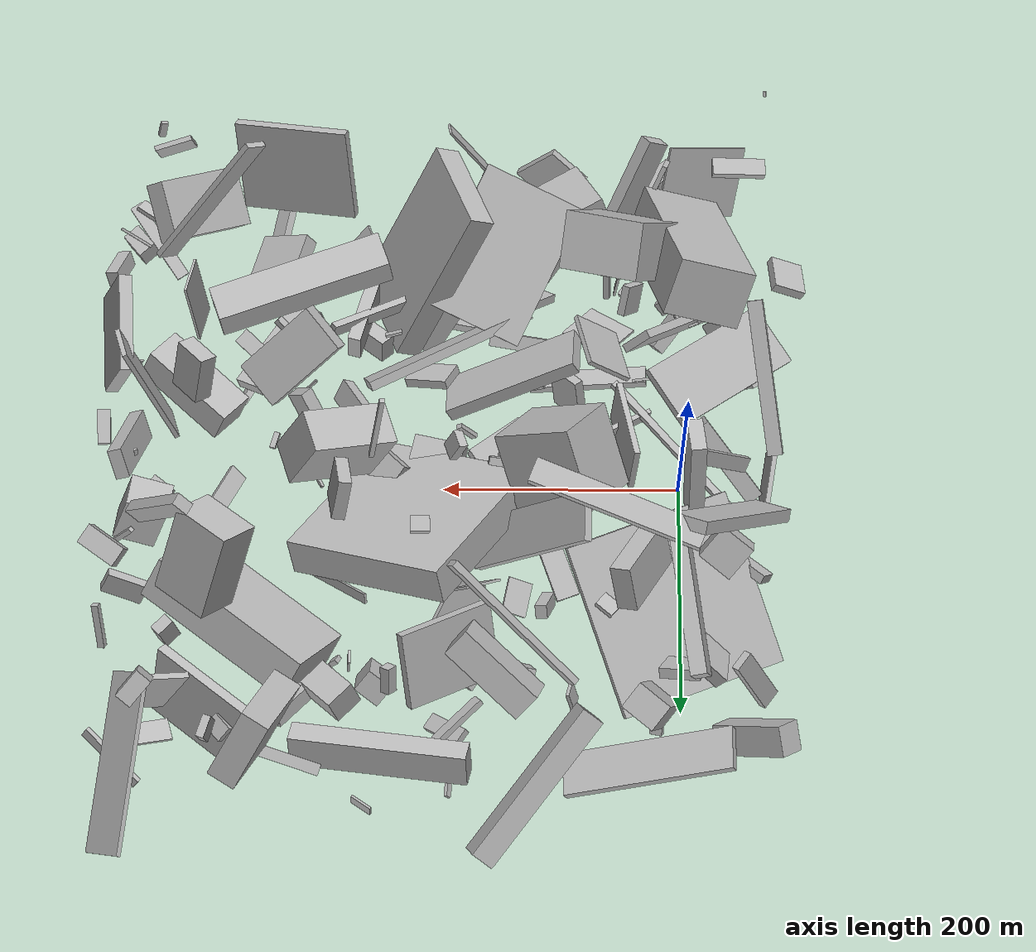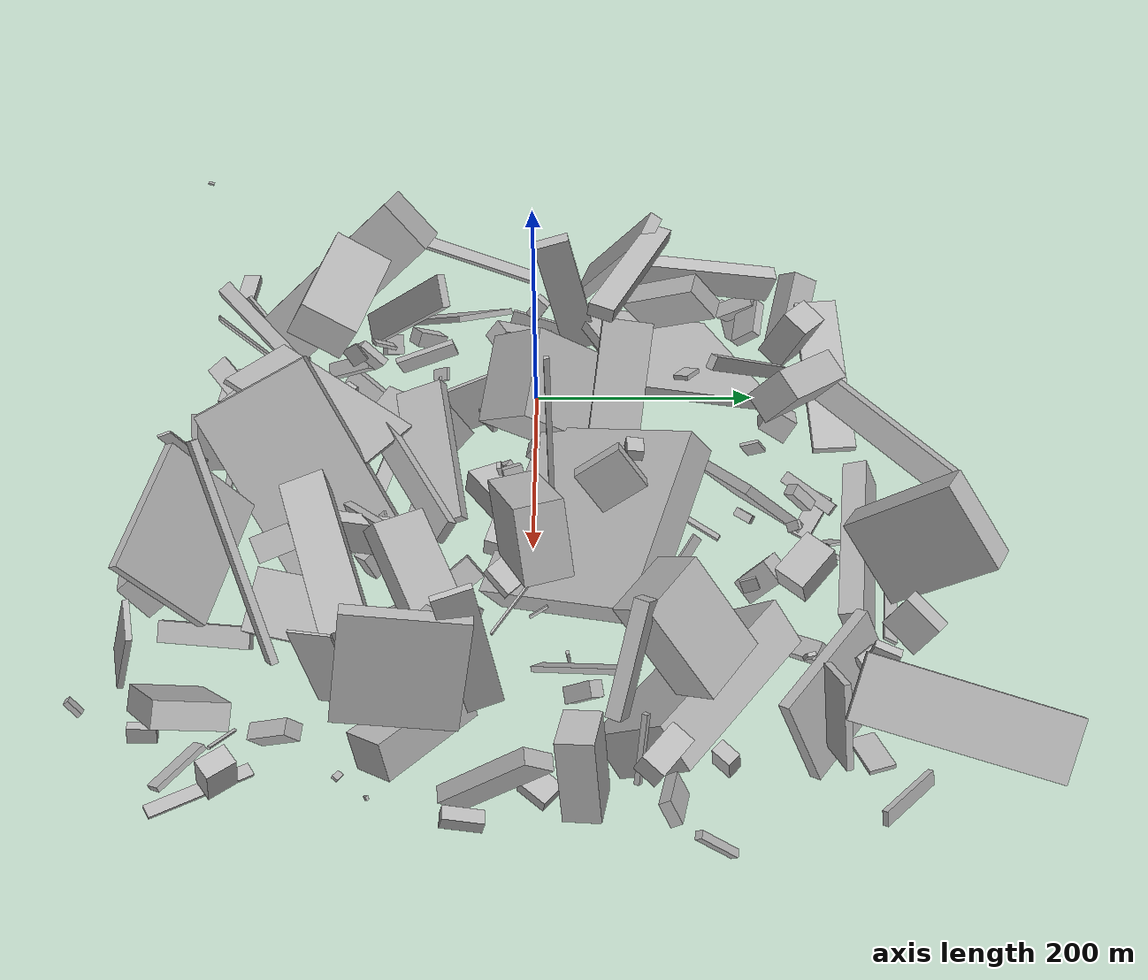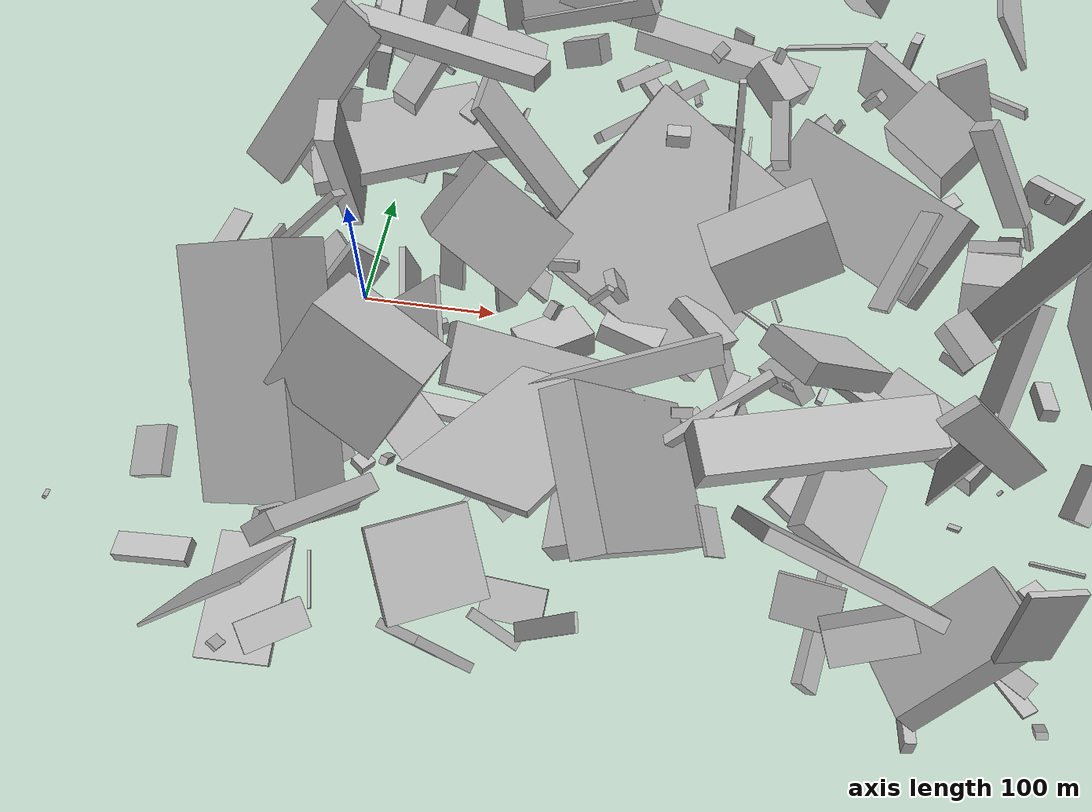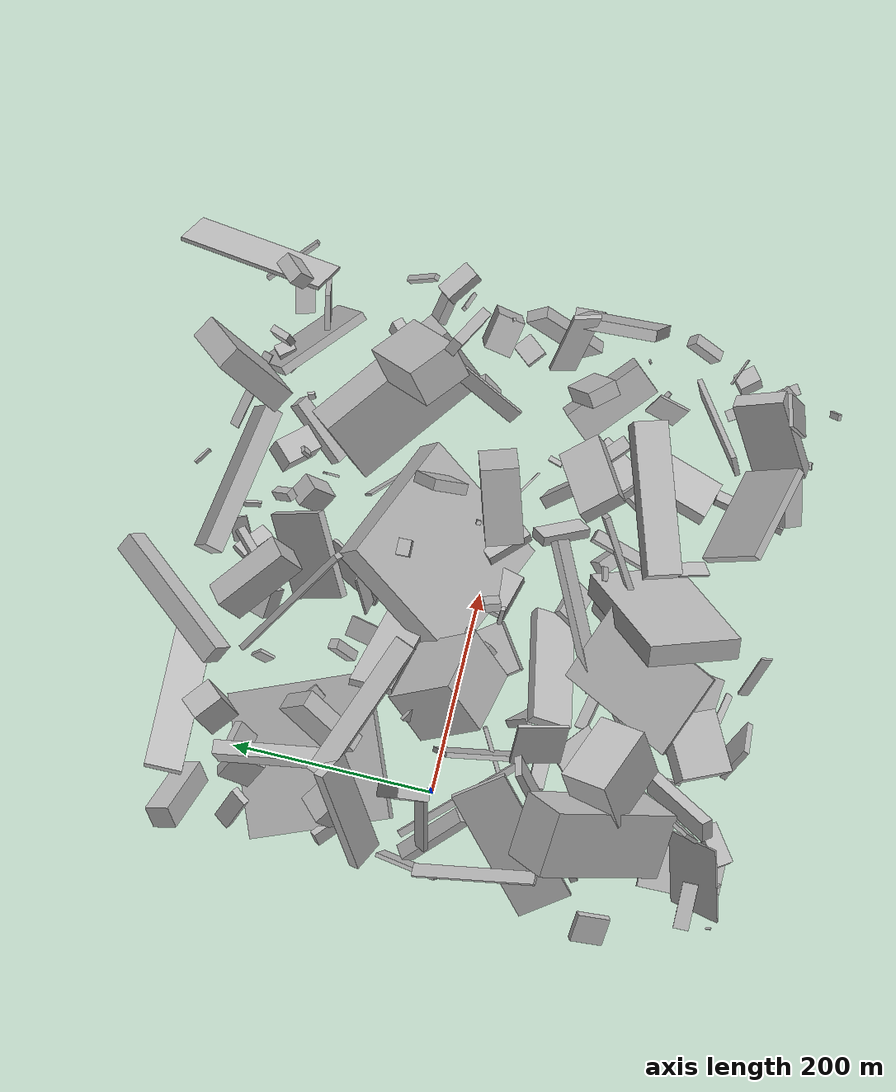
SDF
<sdf version="1.6">
 <world name="default">
  <scene>
   <sky><clouds><speed>12</speed></clouds></sky>
   <ambient>0.4 0.4 0.4 1</ambient>
   <background>0.7 0.7 0.7 1</background>
   <shadows>1</shadows>
  </scene>
  <gravity>0 0 -9.8066</gravity>
  <magnetic_field>6e-06 2.3e-05 -4.2e-05</magnetic_field>
  <physics default="0" name="default_physics" type="ode">
   <ode>
    <solver>
     <type>quick</type>
     <iters>10</iters>
     <sor>1.0</sor>
     <use_dynamic_moi_rescaling>0</use_dynamic_moi_rescaling>
    </solver>
    <constraints>
     <cfm>0</cfm>
     <erp>0.2</erp>
     <contact_max_correcting_vel>100</contact_max_correcting_vel>
     <contact_surface_layer>0.001</contact_surface_layer>
    </constraints>
   </ode>
   <max_step_size>0.004</max_step_size>
   <real_time_factor>1</real_time_factor>
   <real_time_update_rate>250</real_time_update_rate>
  </physics>
  <light name="sun" type="directional">
   <pose>0 0 10 0 0 0</pose>
   <diffuse>0.8 0.8 0.8 1</diffuse>
   <specular>0.2 0.2 0.2 1</specular>
   <attenuation>
    <range>1000</range>
    <constant>0.9</constant>
    <linear>0.01</linear>
    <quadratic>0.001</quadratic>
   </attenuation>
   <direction>-0.5 0.1 -0.9</direction>
  </light>
  <model name="building_1">
   <static>0</static>
   <pose>264.849977985416 106.44058181233544 84.6204089097445 -2.01697700280411 -0.44693034375789936 2.7563679451558456</pose>
   <link name="link">
    <gravity>0</gravity>
    <pose>0 0 75.0 0 0 0</pose>
    <collision name="collision"><geometry><box><size>150 31 150</size></box></geometry></collision>
    <visual name="visual">
     <cast_shadows>0</cast_shadows>
     <geometry><box><size>150 31 150</size></box></geometry>
     <material>
      <script>
       <uri>model://HANNAS_wall/materials/scripts</uri>
       <uri>model://HANNAS_wall/materials/textures</uri>
       <name>vrc/HANNAS_wall</name>
      </script>
     </material>
    </visual>
   </link>
  </model>
  <model name="building_2">
   <static>0</static>
   <pose>121.67454293645461 -74.24415346656589 50.2734152597386 0.9018676148814514 -1.2060296102163366 0.769869163232745</pose>
   <link name="link">
    <gravity>0</gravity>
    <pose>0 0 3.0 0 0 0</pose>
    <collision name="collision"><geometry><box><size>24 10 6</size></box></geometry></collision>
    <visual name="visual">
     <cast_shadows>0</cast_shadows>
     <geometry><box><size>24 10 6</size></box></geometry>
     <material>
      <script>
       <uri>model://HANNAS_wall/materials/scripts</uri>
       <uri>model://HANNAS_wall/materials/textures</uri>
       <name>vrc/HANNAS_wall</name>
      </script>
     </material>
    </visual>
   </link>
  </model>
  <model name="building_3">
   <static>0</static>
   <pose>263.7009953151315 -63.7383196793424 79.46305641383938 1.553918782447553 -0.6286492865791705 -1.1026360040005647</pose>
   <link name="link">
    <gravity>0</gravity>
    <pose>0 0 75.0 0 0 0</pose>
    <collision name="collision"><geometry><box><size>8 20 150</size></box></geometry></collision>
    <visual name="visual">
     <cast_shadows>0</cast_shadows>
     <geometry><box><size>8 20 150</size></box></geometry>
     <material>
      <script>
       <uri>model://HANNAS_wall/materials/scripts</uri>
       <uri>model://HANNAS_wall/materials/textures</uri>
       <name>vrc/HANNAS_wall</name>
      </script>
     </material>
    </visual>
   </link>
  </model>
  <model name="building_4">
   <static>0</static>
   <pose>78.47049025315252 230.7935827755217 90.27862806128 1.9296425669540433 0.5133048657004172 2.638797281294016</pose>
   <link name="link">
    <gravity>0</gravity>
    <pose>0 0 75.0 0 0 0</pose>
    <collision name="collision"><geometry><box><size>21 23 150</size></box></geometry></collision>
    <visual name="visual">
     <cast_shadows>0</cast_shadows>
     <geometry><box><size>21 23 150</size></box></geometry>
     <material>
      <script>
       <uri>model://HANNAS_wall/materials/scripts</uri>
       <uri>model://HANNAS_wall/materials/textures</uri>
       <name>vrc/HANNAS_wall</name>
      </script>
     </material>
    </visual>
   </link>
  </model>
  <model name="building_5">
   <static>0</static>
   <pose>128.24079163408467 69.52383484495557 87.54424538794112 2.210367759030449 -0.14760717539159557 -1.586582268303358</pose>
   <link name="link">
    <gravity>0</gravity>
    <pose>0 0 3.5 0 0 0</pose>
    <collision name="collision"><geometry><box><size>42 150 7</size></box></geometry></collision>
    <visual name="visual">
     <cast_shadows>0</cast_shadows>
     <geometry><box><size>42 150 7</size></box></geometry>
     <material>
      <script>
       <uri>model://HANNAS_wall/materials/scripts</uri>
       <uri>model://HANNAS_wall/materials/textures</uri>
       <name>vrc/HANNAS_wall</name>
      </script>
     </material>
    </visual>
   </link>
  </model>
  <model name="building_6">
   <static>0</static>
   <pose>383.94399075331796 95.2214970999192 106.78039868104145 0.9339067111695544 -0.1903255971860133 2.4547610325015774</pose>
   <link name="link">
    <gravity>0</gravity>
    <pose>0 0 20.0 0 0 0</pose>
    <collision name="collision"><geometry><box><size>52 79 40</size></box></geometry></collision>
    <visual name="visual">
     <cast_shadows>0</cast_shadows>
     <geometry><box><size>52 79 40</size></box></geometry>
     <material>
      <script>
       <uri>model://HANNAS_wall/materials/scripts</uri>
       <uri>model://HANNAS_wall/materials/textures</uri>
       <name>vrc/HANNAS_wall</name>
      </script>
     </material>
    </visual>
   </link>
  </model>
  <model name="building_7">
   <static>0</static>
   <pose>33.65582038439773 128.1588412073554 117.12757634830288 -0.5220257955210924 -0.395185563389628 2.862511263472836</pose>
   <link name="link">
    <gravity>0</gravity>
    <pose>0 0 20.0 0 0 0</pose>
    <collision name="collision"><geometry><box><size>18 71 40</size></box></geometry></collision>
    <visual name="visual">
     <cast_shadows>0</cast_shadows>
     <geometry><box><size>18 71 40</size></box></geometry>
     <material>
      <script>
       <uri>model://HANNAS_wall/materials/scripts</uri>
       <uri>model://HANNAS_wall/materials/textures</uri>
       <name>vrc/HANNAS_wall</name>
      </script>
     </material>
    </visual>
   </link>
  </model>
  <model name="building_8">
   <static>0</static>
   <pose>385.1747498785552 144.99763910502327 49.589972824680885 2.3259016913742108 -0.023929955335914098 -0.6515366699318969</pose>
   <link name="link">
    <gravity>0</gravity>
    <pose>0 0 38.0 0 0 0</pose>
    <collision name="collision"><geometry><box><size>150 38 76</size></box></geometry></collision>
    <visual name="visual">
     <cast_shadows>0</cast_shadows>
     <geometry><box><size>150 38 76</size></box></geometry>
     <material>
      <script>
       <uri>model://HANNAS_wall/materials/scripts</uri>
       <uri>model://HANNAS_wall/materials/textures</uri>
       <name>vrc/HANNAS_wall</name>
      </script>
     </material>
    </visual>
   </link>
  </model>
  <model name="building_9">
   <static>0</static>
   <pose>405.140047572476 -216.71154803683282 47.58208503096767 1.086932046682388 -0.6461641095841756 0.5884371205439956</pose>
   <link name="link">
    <gravity>0</gravity>
    <pose>0 0 25.5 0 0 0</pose>
    <collision name="collision"><geometry><box><size>91 19 51</size></box></geometry></collision>
    <visual name="visual">
     <cast_shadows>0</cast_shadows>
     <geometry><box><size>91 19 51</size></box></geometry>
     <material>
      <script>
       <uri>model://HANNAS_wall/materials/scripts</uri>
       <uri>model://HANNAS_wall/materials/textures</uri>
       <name>vrc/HANNAS_wall</name>
      </script>
     </material>
    </visual>
   </link>
  </model>
  <model name="building_10">
   <static>0</static>
   <pose>-33.84356640902685 -87.4722660566936 70.33140518814417 -2.861158219700162 0.5132305663151959 -2.3832899114575237</pose>
   <link name="link">
    <gravity>0</gravity>
    <pose>0 0 2.5 0 0 0</pose>
    <collision name="collision"><geometry><box><size>150 56 5</size></box></geometry></collision>
    <visual name="visual">
     <cast_shadows>0</cast_shadows>
     <geometry><box><size>150 56 5</size></box></geometry>
     <material>
      <script>
       <uri>model://HANNAS_wall/materials/scripts</uri>
       <uri>model://HANNAS_wall/materials/textures</uri>
       <name>vrc/HANNAS_wall</name>
      </script>
     </material>
    </visual>
   </link>
  </model>
  <model name="building_11">
   <static>0</static>
   <pose>140.59215792475706 -104.03305436627477 42.69475707253159 0.8491979033820337 0.8985987696537667 2.490434043281318</pose>
   <link name="link">
    <gravity>0</gravity>
    <pose>0 0 21.0 0 0 0</pose>
    <collision name="collision"><geometry><box><size>12 123 42</size></box></geometry></collision>
    <visual name="visual">
     <cast_shadows>0</cast_shadows>
     <geometry><box><size>12 123 42</size></box></geometry>
     <material>
      <script>
       <uri>model://HANNAS_wall/materials/scripts</uri>
       <uri>model://HANNAS_wall/materials/textures</uri>
       <name>vrc/HANNAS_wall</name>
      </script>
     </material>
    </visual>
   </link>
  </model>
  <model name="building_12">
   <static>0</static>
   <pose>341.77327653657176 -40.976510238996866 7.428254835937576 1.727025056933067 0.1631977609604627 1.2708965915113848</pose>
   <link name="link">
    <gravity>0</gravity>
    <pose>0 0 2.5 0 0 0</pose>
    <collision name="collision"><geometry><box><size>14 4 5</size></box></geometry></collision>
    <visual name="visual">
     <cast_shadows>0</cast_shadows>
     <geometry><box><size>14 4 5</size></box></geometry>
     <material>
      <script>
       <uri>model://HANNAS_wall/materials/scripts</uri>
       <uri>model://HANNAS_wall/materials/textures</uri>
       <name>vrc/HANNAS_wall</name>
      </script>
     </material>
    </visual>
   </link>
  </model>
  <model name="building_13">
   <static>0</static>
   <pose>122.49739351463079 -171.38835465769185 32.34084828139092 0.8966993625877948 -0.418414041197858 2.5714429312567724</pose>
   <link name="link">
    <gravity>0</gravity>
    <pose>0 0 33.5 0 0 0</pose>
    <collision name="collision"><geometry><box><size>43 7 67</size></box></geometry></collision>
    <visual name="visual">
     <cast_shadows>0</cast_shadows>
     <geometry><box><size>43 7 67</size></box></geometry>
     <material>
      <script>
       <uri>model://HANNAS_wall/materials/scripts</uri>
       <uri>model://HANNAS_wall/materials/textures</uri>
       <name>vrc/HANNAS_wall</name>
      </script>
     </material>
    </visual>
   </link>
  </model>
  <model name="building_14">
   <static>0</static>
   <pose>-15.436032207418005 27.245005368923195 110.64087493631567 1.5579793545809095 -0.2396758570967066 1.6798934542473338</pose>
   <link name="link">
    <gravity>0</gravity>
    <pose>0 0 6.5 0 0 0</pose>
    <collision name="collision"><geometry><box><size>31 113 13</size></box></geometry></collision>
    <visual name="visual">
     <cast_shadows>0</cast_shadows>
     <geometry><box><size>31 113 13</size></box></geometry>
     <material>
      <script>
       <uri>model://HANNAS_wall/materials/scripts</uri>
       <uri>model://HANNAS_wall/materials/textures</uri>
       <name>vrc/HANNAS_wall</name>
      </script>
     </material>
    </visual>
   </link>
  </model>
  <model name="building_15">
   <static>0</static>
   <pose>112.00935101478676 -19.035828653204476 113.4393566233634 -2.3747816115167866 -0.5565827407260263 0.8830065642503457</pose>
   <link name="link">
    <gravity>0</gravity>
    <pose>0 0 36.5 0 0 0</pose>
    <collision name="collision"><geometry><box><size>60 75 73</size></box></geometry></collision>
    <visual name="visual">
     <cast_shadows>0</cast_shadows>
     <geometry><box><size>60 75 73</size></box></geometry>
     <material>
      <script>
       <uri>model://HANNAS_wall/materials/scripts</uri>
       <uri>model://HANNAS_wall/materials/textures</uri>
       <name>vrc/HANNAS_wall</name>
      </script>
     </material>
    </visual>
   </link>
  </model>
  <model name="building_16">
   <static>0</static>
   <pose>313.4151675149286 193.3849812421438 20.165825439241175 -2.1046970946129013 0.311330232934953 -2.2739135589272155</pose>
   <link name="link">
    <gravity>0</gravity>
    <pose>0 0 7.5 0 0 0</pose>
    <collision name="collision"><geometry><box><size>71 13 15</size></box></geometry></collision>
    <visual name="visual">
     <cast_shadows>0</cast_shadows>
     <geometry><box><size>71 13 15</size></box></geometry>
     <material>
      <script>
       <uri>model://HANNAS_wall/materials/scripts</uri>
       <uri>model://HANNAS_wall/materials/textures</uri>
       <name>vrc/HANNAS_wall</name>
      </script>
     </material>
    </visual>
   </link>
  </model>
  <model name="building_17">
   <static>0</static>
   <pose>192.8419064176132 171.6175921665391 61.63886170789642 2.2914259539188766 -0.2971018441356968 0.5050845875066865</pose>
   <link name="link">
    <gravity>0</gravity>
    <pose>0 0 4.0 0 0 0</pose>
    <collision name="collision"><geometry><box><size>87 68 8</size></box></geometry></collision>
    <visual name="visual">
     <cast_shadows>0</cast_shadows>
     <geometry><box><size>87 68 8</size></box></geometry>
     <material>
      <script>
       <uri>model://HANNAS_wall/materials/scripts</uri>
       <uri>model://HANNAS_wall/materials/textures</uri>
       <name>vrc/HANNAS_wall</name>
      </script>
     </material>
    </visual>
   </link>
  </model>
  <model name="building_18">
   <static>0</static>
   <pose>229.438580512625 -218.84862247146435 82.03777146807872 0.9580243260923124 -0.8941822869639865 -2.295074446855041</pose>
   <link name="link">
    <gravity>0</gravity>
    <pose>0 0 47.0 0 0 0</pose>
    <collision name="collision"><geometry><box><size>150 22 94</size></box></geometry></collision>
    <visual name="visual">
     <cast_shadows>0</cast_shadows>
     <geometry><box><size>150 22 94</size></box></geometry>
     <material>
      <script>
       <uri>model://HANNAS_wall/materials/scripts</uri>
       <uri>model://HANNAS_wall/materials/textures</uri>
       <name>vrc/HANNAS_wall</name>
      </script>
     </material>
    </visual>
   </link>
  </model>
  <model name="building_19">
   <static>0</static>
   <pose>254.51070104410957 -120.72596495199232 52.181886951948115 -1.2802996727481015 0.2540777095912527 -0.7292470649710532</pose>
   <link name="link">
    <gravity>0</gravity>
    <pose>0 0 7.0 0 0 0</pose>
    <collision name="collision"><geometry><box><size>32 21 14</size></box></geometry></collision>
    <visual name="visual">
     <cast_shadows>0</cast_shadows>
     <geometry><box><size>32 21 14</size></box></geometry>
     <material>
      <script>
       <uri>model://HANNAS_wall/materials/scripts</uri>
       <uri>model://HANNAS_wall/materials/textures</uri>
       <name>vrc/HANNAS_wall</name>
      </script>
     </material>
    </visual>
   </link>
  </model>
  <model name="building_20">
   <static>0</static>
   <pose>191.8151705351303 -170.61002182184933 29.73649728805219 0.11571769139053964 0.5264253283822369 -3.0872620706388156</pose>
   <link name="link">
    <gravity>0</gravity>
    <pose>0 0 7.5 0 0 0</pose>
    <collision name="collision"><geometry><box><size>40 67 15</size></box></geometry></collision>
    <visual name="visual">
     <cast_shadows>0</cast_shadows>
     <geometry><box><size>40 67 15</size></box></geometry>
     <material>
      <script>
       <uri>model://HANNAS_wall/materials/scripts</uri>
       <uri>model://HANNAS_wall/materials/textures</uri>
       <name>vrc/HANNAS_wall</name>
      </script>
     </material>
    </visual>
   </link>
  </model>
  <model name="building_21">
   <static>0</static>
   <pose>-52.05956634757235 244.55013304726754 60.452595898819254 -2.41722536001845 -0.7011780011076999 2.828474958927994</pose>
   <link name="link">
    <gravity>0</gravity>
    <pose>0 0 12.0 0 0 0</pose>
    <collision name="collision"><geometry><box><size>71 26 24</size></box></geometry></collision>
    <visual name="visual">
     <cast_shadows>0</cast_shadows>
     <geometry><box><size>71 26 24</size></box></geometry>
     <material>
      <script>
       <uri>model://HANNAS_wall/materials/scripts</uri>
       <uri>model://HANNAS_wall/materials/textures</uri>
       <name>vrc/HANNAS_wall</name>
      </script>
     </material>
    </visual>
   </link>
  </model>
  <model name="building_22">
   <static>0</static>
   <pose>49.111405487211826 -192.21956928621262 51.790322311394625 -0.8006094675814664 0.13518739628299245 2.722499859633222</pose>
   <link name="link">
    <gravity>0</gravity>
    <pose>0 0 48.5 0 0 0</pose>
    <collision name="collision"><geometry><box><size>4 18 97</size></box></geometry></collision>
    <visual name="visual">
     <cast_shadows>0</cast_shadows>
     <geometry><box><size>4 18 97</size></box></geometry>
     <material>
      <script>
       <uri>model://HANNAS_wall/materials/scripts</uri>
       <uri>model://HANNAS_wall/materials/textures</uri>
       <name>vrc/HANNAS_wall</name>
      </script>
     </material>
    </visual>
   </link>
  </model>
  <model name="building_23">
   <static>0</static>
   <pose>58.527197375153605 -203.75554127191376 84.30157970261227 0.5784418254748094 -0.742789438508489 0.26980000603774135</pose>
   <link name="link">
    <gravity>0</gravity>
    <pose>0 0 44.5 0 0 0</pose>
    <collision name="collision"><geometry><box><size>22 12 89</size></box></geometry></collision>
    <visual name="visual">
     <cast_shadows>0</cast_shadows>
     <geometry><box><size>22 12 89</size></box></geometry>
     <material>
      <script>
       <uri>model://HANNAS_wall/materials/scripts</uri>
       <uri>model://HANNAS_wall/materials/textures</uri>
       <name>vrc/HANNAS_wall</name>
      </script>
     </material>
    </visual>
   </link>
  </model>
  <model name="building_24">
   <static>0</static>
   <pose>101.99166692213082 2.2670807623481766 21.442769774563462 2.1508957000983564 -1.1363727829226282 1.8044100079217842</pose>
   <link name="link">
    <gravity>0</gravity>
    <pose>0 0 8.5 0 0 0</pose>
    <collision name="collision"><geometry><box><size>28 4 17</size></box></geometry></collision>
    <visual name="visual">
     <cast_shadows>0</cast_shadows>
     <geometry><box><size>28 4 17</size></box></geometry>
     <material>
      <script>
       <uri>model://HANNAS_wall/materials/scripts</uri>
       <uri>model://HANNAS_wall/materials/textures</uri>
       <name>vrc/HANNAS_wall</name>
      </script>
     </material>
    </visual>
   </link>
  </model>
  <model name="building_25">
   <static>0</static>
   <pose>322.5534758752127 -145.5366315214743 120.0016162553365 3.070965974423638 0.2050050162856617 -1.262281968577617</pose>
   <link name="link">
    <gravity>0</gravity>
    <pose>0 0 12.0 0 0 0</pose>
    <collision name="collision"><geometry><box><size>34 150 24</size></box></geometry></collision>
    <visual name="visual">
     <cast_shadows>0</cast_shadows>
     <geometry><box><size>34 150 24</size></box></geometry>
     <material>
      <script>
       <uri>model://HANNAS_wall/materials/scripts</uri>
       <uri>model://HANNAS_wall/materials/textures</uri>
       <name>vrc/HANNAS_wall</name>
      </script>
     </material>
    </visual>
   </link>
  </model>
  <model name="building_26">
   <static>0</static>
   <pose>351.94292441095604 -122.14357779134224 28.229616938424634 -0.21927653988342435 1.185726907733517 2.3750195157393765</pose>
   <link name="link">
    <gravity>0</gravity>
    <pose>0 0 15.0 0 0 0</pose>
    <collision name="collision"><geometry><box><size>10 89 30</size></box></geometry></collision>
    <visual name="visual">
     <cast_shadows>0</cast_shadows>
     <geometry><box><size>10 89 30</size></box></geometry>
     <material>
      <script>
       <uri>model://HANNAS_wall/materials/scripts</uri>
       <uri>model://HANNAS_wall/materials/textures</uri>
       <name>vrc/HANNAS_wall</name>
      </script>
     </material>
    </visual>
   </link>
  </model>
  <model name="building_27">
   <static>0</static>
   <pose>300.19884573186056 4.540060153854442 81.78005194714694 0.0020173243054772043 -0.4248302830568203 0.30948812837808026</pose>
   <link name="link">
    <gravity>0</gravity>
    <pose>0 0 29.5 0 0 0</pose>
    <collision name="collision"><geometry><box><size>77 37 59</size></box></geometry></collision>
    <visual name="visual">
     <cast_shadows>0</cast_shadows>
     <geometry><box><size>77 37 59</size></box></geometry>
     <material>
      <script>
       <uri>model://HANNAS_wall/materials/scripts</uri>
       <uri>model://HANNAS_wall/materials/textures</uri>
       <name>vrc/HANNAS_wall</name>
      </script>
     </material>
    </visual>
   </link>
  </model>
  <model name="building_28">
   <static>0</static>
   <pose>250.27088266069612 175.07507582274286 27.637888533658046 -2.1757383056054986 -0.37748198373114317 -0.5509081720300691</pose>
   <link name="link">
    <gravity>0</gravity>
    <pose>0 0 10.5 0 0 0</pose>
    <collision name="collision"><geometry><box><size>24 32 21</size></box></geometry></collision>
    <visual name="visual">
     <cast_shadows>0</cast_shadows>
     <geometry><box><size>24 32 21</size></box></geometry>
     <material>
      <script>
       <uri>model://HANNAS_wall/materials/scripts</uri>
       <uri>model://HANNAS_wall/materials/textures</uri>
       <name>vrc/HANNAS_wall</name>
      </script>
     </material>
    </visual>
   </link>
  </model>
  <model name="building_29">
   <static>0</static>
   <pose>28.567235247773425 277.4853216290534 49.68945532320822 -1.7116640859551067 1.160692861656665 3.0284431751093934</pose>
   <link name="link">
    <gravity>0</gravity>
    <pose>0 0 18.5 0 0 0</pose>
    <collision name="collision"><geometry><box><size>8 150 37</size></box></geometry></collision>
    <visual name="visual">
     <cast_shadows>0</cast_shadows>
     <geometry><box><size>8 150 37</size></box></geometry>
     <material>
      <script>
       <uri>model://HANNAS_wall/materials/scripts</uri>
       <uri>model://HANNAS_wall/materials/textures</uri>
       <name>vrc/HANNAS_wall</name>
      </script>
     </material>
    </visual>
   </link>
  </model>
  <model name="building_30">
   <static>0</static>
   <pose>-79.44145912278564 -179.95170900106856 52.76098043010613 -2.058156387643517 -0.3395776187814273 1.651887740732104</pose>
   <link name="link">
    <gravity>0</gravity>
    <pose>0 0 14.5 0 0 0</pose>
    <collision name="collision"><geometry><box><size>33 8 29</size></box></geometry></collision>
    <visual name="visual">
     <cast_shadows>0</cast_shadows>
     <geometry><box><size>33 8 29</size></box></geometry>
     <material>
      <script>
       <uri>model://HANNAS_wall/materials/scripts</uri>
       <uri>model://HANNAS_wall/materials/textures</uri>
       <name>vrc/HANNAS_wall</name>
      </script>
     </material>
    </visual>
   </link>
  </model>
  <model name="building_31">
   <static>0</static>
   <pose>478.80490878973114 -157.00881452525365 105.79570847653156 -1.1338721874667617 -0.5250009167957803 1.238414022761042</pose>
   <link name="link">
    <gravity>0</gravity>
    <pose>0 0 5.5 0 0 0</pose>
    <collision name="collision"><geometry><box><size>33 14 11</size></box></geometry></collision>
    <visual name="visual">
     <cast_shadows>0</cast_shadows>
     <geometry><box><size>33 14 11</size></box></geometry>
     <material>
      <script>
       <uri>model://HANNAS_wall/materials/scripts</uri>
       <uri>model://HANNAS_wall/materials/textures</uri>
       <name>vrc/HANNAS_wall</name>
      </script>
     </material>
    </visual>
   </link>
  </model>
  <model name="building_32">
   <static>0</static>
   <pose>1.5251582114932403 -162.8800857314534 38.95548740673219 0.8877306894256985 -0.4964116806762439 1.1968607025240063</pose>
   <link name="link">
    <gravity>0</gravity>
    <pose>0 0 6.0 0 0 0</pose>
    <collision name="collision"><geometry><box><size>47 13 12</size></box></geometry></collision>
    <visual name="visual">
     <cast_shadows>0</cast_shadows>
     <geometry><box><size>47 13 12</size></box></geometry>
     <material>
      <script>
       <uri>model://HANNAS_wall/materials/scripts</uri>
       <uri>model://HANNAS_wall/materials/textures</uri>
       <name>vrc/HANNAS_wall</name>
      </script>
     </material>
    </visual>
   </link>
  </model>
  <model name="building_33">
   <static>0</static>
   <pose>333.6375676161288 -235.89864007672412 44.265550735526936 0.8222616204111167 -0.0848726247882162 1.3858291198460326</pose>
   <link name="link">
    <gravity>0</gravity>
    <pose>0 0 3.5 0 0 0</pose>
    <collision name="collision"><geometry><box><size>72 16 7</size></box></geometry></collision>
    <visual name="visual">
     <cast_shadows>0</cast_shadows>
     <geometry><box><size>72 16 7</size></box></geometry>
     <material>
      <script>
       <uri>model://HANNAS_wall/materials/scripts</uri>
       <uri>model://HANNAS_wall/materials/textures</uri>
       <name>vrc/HANNAS_wall</name>
      </script>
     </material>
    </visual>
   </link>
  </model>
  <model name="building_34">
   <static>0</static>
   <pose>323.2632670175917 -235.57052752446924 83.41640910326358 0.7910552904471239 -0.17024961377150963 -0.226705672656848</pose>
   <link name="link">
    <gravity>0</gravity>
    <pose>0 0 2.0 0 0 0</pose>
    <collision name="collision"><geometry><box><size>38 28 4</size></box></geometry></collision>
    <visual name="visual">
     <cast_shadows>0</cast_shadows>
     <geometry><box><size>38 28 4</size></box></geometry>
     <material>
      <script>
       <uri>model://HANNAS_wall/materials/scripts</uri>
       <uri>model://HANNAS_wall/materials/textures</uri>
       <name>vrc/HANNAS_wall</name>
      </script>
     </material>
    </visual>
   </link>
  </model>
  <model name="building_35">
   <static>0</static>
   <pose>332.41015357844 -70.02120748040157 78.80988284577822 1.4460304723478818 0.25216577824603664 0.7967283314312058</pose>
   <link name="link">
    <gravity>0</gravity>
    <pose>0 0 26.5 0 0 0</pose>
    <collision name="collision"><geometry><box><size>14 7 53</size></box></geometry></collision>
    <visual name="visual">
     <cast_shadows>0</cast_shadows>
     <geometry><box><size>14 7 53</size></box></geometry>
     <material>
      <script>
       <uri>model://HANNAS_wall/materials/scripts</uri>
       <uri>model://HANNAS_wall/materials/textures</uri>
       <name>vrc/HANNAS_wall</name>
      </script>
     </material>
    </visual>
   </link>
  </model>
  <model name="building_36">
   <static>0</static>
   <pose>-36.95932191100841 -157.59381388682877 120.89456675348643 1.1072825740776007 -0.7057217410574697 1.8087956194452175</pose>
   <link name="link">
    <gravity>0</gravity>
    <pose>0 0 33.0 0 0 0</pose>
    <collision name="collision"><geometry><box><size>150 50 66</size></box></geometry></collision>
    <visual name="visual">
     <cast_shadows>0</cast_shadows>
     <geometry><box><size>150 50 66</size></box></geometry>
     <material>
      <script>
       <uri>model://HANNAS_wall/materials/scripts</uri>
       <uri>model://HANNAS_wall/materials/textures</uri>
       <name>vrc/HANNAS_wall</name>
      </script>
     </material>
    </visual>
   </link>
  </model>
  <model name="building_37">
   <static>0</static>
   <pose>478.90384116490014 72.8757843723613 59.40028169801141 -0.1852054784174409 0.4100559340193807 2.4796875711877697</pose>
   <link name="link">
    <gravity>0</gravity>
    <pose>0 0 25.0 0 0 0</pose>
    <collision name="collision"><geometry><box><size>4 4 50</size></box></geometry></collision>
    <visual name="visual">
     <cast_shadows>0</cast_shadows>
     <geometry><box><size>4 4 50</size></box></geometry>
     <material>
      <script>
       <uri>model://HANNAS_wall/materials/scripts</uri>
       <uri>model://HANNAS_wall/materials/textures</uri>
       <name>vrc/HANNAS_wall</name>
      </script>
     </material>
    </visual>
   </link>
  </model>
  <model name="building_38">
   <static>0</static>
   <pose>188.38997270461024 222.72976155121083 50.627325709774034 2.4270826479740526 -0.08993047776700397 -2.3756900822512206</pose>
   <link name="link">
    <gravity>0</gravity>
    <pose>0 0 2.5 0 0 0</pose>
    <collision name="collision"><geometry><box><size>50 10 5</size></box></geometry></collision>
    <visual name="visual">
     <cast_shadows>0</cast_shadows>
     <geometry><box><size>50 10 5</size></box></geometry>
     <material>
      <script>
       <uri>model://HANNAS_wall/materials/scripts</uri>
       <uri>model://HANNAS_wall/materials/textures</uri>
       <name>vrc/HANNAS_wall</name>
      </script>
     </material>
    </visual>
   </link>
  </model>
  <model name="building_39">
   <static>0</static>
   <pose>2.3936040287253206 -34.55458447452567 18.436485239203073 0.48066200383266544 -1.20341267101894 -2.8373235764339726</pose>
   <link name="link">
    <gravity>0</gravity>
    <pose>0 0 3.5 0 0 0</pose>
    <collision name="collision"><geometry><box><size>4 150 7</size></box></geometry></collision>
    <visual name="visual">
     <cast_shadows>0</cast_shadows>
     <geometry><box><size>4 150 7</size></box></geometry>
     <material>
      <script>
       <uri>model://HANNAS_wall/materials/scripts</uri>
       <uri>model://HANNAS_wall/materials/textures</uri>
       <name>vrc/HANNAS_wall</name>
      </script>
     </material>
    </visual>
   </link>
  </model>
  <model name="building_40">
   <static>0</static>
   <pose>426.83276334786706 -27.397830946614157 76.91111092455172 -0.15695904461921084 -0.20760866715655382 -2.8284619883293396</pose>
   <link name="link">
    <gravity>0</gravity>
    <pose>0 0 75.0 0 0 0</pose>
    <collision name="collision"><geometry><box><size>4 26 150</size></box></geometry></collision>
    <visual name="visual">
     <cast_shadows>0</cast_shadows>
     <geometry><box><size>4 26 150</size></box></geometry>
     <material>
      <script>
       <uri>model://HANNAS_wall/materials/scripts</uri>
       <uri>model://HANNAS_wall/materials/textures</uri>
       <name>vrc/HANNAS_wall</name>
      </script>
     </material>
    </visual>
   </link>
  </model>
  <model name="building_41">
   <static>0</static>
   <pose>0.4950974912496222 -116.40774191293919 99.51234034959154 -1.8950682909638612 -0.718082350823617 0.7394031155737554</pose>
   <link name="link">
    <gravity>0</gravity>
    <pose>0 0 3.5 0 0 0</pose>
    <collision name="collision"><geometry><box><size>150 28 7</size></box></geometry></collision>
    <visual name="visual">
     <cast_shadows>0</cast_shadows>
     <geometry><box><size>150 28 7</size></box></geometry>
     <material>
      <script>
       <uri>model://HANNAS_wall/materials/scripts</uri>
       <uri>model://HANNAS_wall/materials/textures</uri>
       <name>vrc/HANNAS_wall</name>
      </script>
     </material>
    </visual>
   </link>
  </model>
  <model name="building_42">
   <static>0</static>
   <pose>-24.606994990017707 103.51368211834578 100.1238227056974 -0.5710644936701937 -0.9394448603496097 1.4514879218049381</pose>
   <link name="link">
    <gravity>0</gravity>
    <pose>0 0 16.0 0 0 0</pose>
    <collision name="collision"><geometry><box><size>23 32 32</size></box></geometry></collision>
    <visual name="visual">
     <cast_shadows>0</cast_shadows>
     <geometry><box><size>23 32 32</size></box></geometry>
     <material>
      <script>
       <uri>model://HANNAS_wall/materials/scripts</uri>
       <uri>model://HANNAS_wall/materials/textures</uri>
       <name>vrc/HANNAS_wall</name>
      </script>
     </material>
    </visual>
   </link>
  </model>
  <model name="building_43">
   <static>0</static>
   <pose>268.15266155838833 -123.83561956874752 97.8906930115783 -3.121774283335875 -0.08569690282155046 1.2927585238035717</pose>
   <link name="link">
    <gravity>0</gravity>
    <pose>0 0 15.5 0 0 0</pose>
    <collision name="collision"><geometry><box><size>57 11 31</size></box></geometry></collision>
    <visual name="visual">
     <cast_shadows>0</cast_shadows>
     <geometry><box><size>57 11 31</size></box></geometry>
     <material>
      <script>
       <uri>model://HANNAS_wall/materials/scripts</uri>
       <uri>model://HANNAS_wall/materials/textures</uri>
       <name>vrc/HANNAS_wall</name>
      </script>
     </material>
    </visual>
   </link>
  </model>
  <model name="building_44">
   <static>0</static>
   <pose>358.9105647196109 -174.12950603644848 65.70686040776827 -0.06546595034180763 0.9545399532808901 2.7904474787112816</pose>
   <link name="link">
    <gravity>0</gravity>
    <pose>0 0 23.5 0 0 0</pose>
    <collision name="collision"><geometry><box><size>14 60 47</size></box></geometry></collision>
    <visual name="visual">
     <cast_shadows>0</cast_shadows>
     <geometry><box><size>14 60 47</size></box></geometry>
     <material>
      <script>
       <uri>model://HANNAS_wall/materials/scripts</uri>
       <uri>model://HANNAS_wall/materials/textures</uri>
       <name>vrc/HANNAS_wall</name>
      </script>
     </material>
    </visual>
   </link>
  </model>
  <model name="building_45">
   <static>0</static>
   <pose>127.72950624329128 -43.83702198578652 17.342487761144245 1.8648189610550907 -1.3908175962853004 1.8951318731811575</pose>
   <link name="link">
    <gravity>0</gravity>
    <pose>0 0 25.5 0 0 0</pose>
    <collision name="collision"><geometry><box><size>20 33 51</size></box></geometry></collision>
    <visual name="visual">
     <cast_shadows>0</cast_shadows>
     <geometry><box><size>20 33 51</size></box></geometry>
     <material>
      <script>
       <uri>model://HANNAS_wall/materials/scripts</uri>
       <uri>model://HANNAS_wall/materials/textures</uri>
       <name>vrc/HANNAS_wall</name>
      </script>
     </material>
    </visual>
   </link>
  </model>
  <model name="building_46">
   <static>0</static>
   <pose>-37.46725545440586 -17.98908160519417 34.09203402637856 0.6190706177024311 -0.2816025937281326 -2.550592374504192</pose>
   <link name="link">
    <gravity>0</gravity>
    <pose>0 0 9.5 0 0 0</pose>
    <collision name="collision"><geometry><box><size>15 81 19</size></box></geometry></collision>
    <visual name="visual">
     <cast_shadows>0</cast_shadows>
     <geometry><box><size>15 81 19</size></box></geometry>
     <material>
      <script>
       <uri>model://HANNAS_wall/materials/scripts</uri>
       <uri>model://HANNAS_wall/materials/textures</uri>
       <name>vrc/HANNAS_wall</name>
      </script>
     </material>
    </visual>
   </link>
  </model>
  <model name="building_47">
   <static>0</static>
   <pose>279.42964077593916 58.84632375753875 151.57569232297772 1.2205018397641232 0.9221992203990589 1.2761099600544</pose>
   <link name="link">
    <gravity>0</gravity>
    <pose>0 0 5.5 0 0 0</pose>
    <collision name="collision"><geometry><box><size>36 38 11</size></box></geometry></collision>
    <visual name="visual">
     <cast_shadows>0</cast_shadows>
     <geometry><box><size>36 38 11</size></box></geometry>
     <material>
      <script>
       <uri>model://HANNAS_wall/materials/scripts</uri>
       <uri>model://HANNAS_wall/materials/textures</uri>
       <name>vrc/HANNAS_wall</name>
      </script>
     </material>
    </visual>
   </link>
  </model>
  <model name="building_48">
   <static>0</static>
   <pose>491.85999937119203 113.64472242578276 21.357083650907377 2.7595846978810323 0.6568551749512188 -1.9767523282468153</pose>
   <link name="link">
    <gravity>0</gravity>
    <pose>0 0 20.0 0 0 0</pose>
    <collision name="collision"><geometry><box><size>6 6 40</size></box></geometry></collision>
    <visual name="visual">
     <cast_shadows>0</cast_shadows>
     <geometry><box><size>6 6 40</size></box></geometry>
     <material>
      <script>
       <uri>model://HANNAS_wall/materials/scripts</uri>
       <uri>model://HANNAS_wall/materials/textures</uri>
       <name>vrc/HANNAS_wall</name>
      </script>
     </material>
    </visual>
   </link>
  </model>
  <model name="building_49">
   <static>0</static>
   <pose>467.4311597780821 94.81520644377954 24.298497867078407 -0.6224199346196262 0.9224113538434442 0.8329217152398347</pose>
   <link name="link">
    <gravity>0</gravity>
    <pose>0 0 4.5 0 0 0</pose>
    <collision name="collision"><geometry><box><size>19 36 9</size></box></geometry></collision>
    <visual name="visual">
     <cast_shadows>0</cast_shadows>
     <geometry><box><size>19 36 9</size></box></geometry>
     <material>
      <script>
       <uri>model://HANNAS_wall/materials/scripts</uri>
       <uri>model://HANNAS_wall/materials/textures</uri>
       <name>vrc/HANNAS_wall</name>
      </script>
     </material>
    </visual>
   </link>
  </model>
  <model name="building_50">
   <static>0</static>
   <pose>436.1111181656753 184.8401235655158 45.52982840303271 -1.1403158247743472 1.1570768370420978 1.2620464149353214</pose>
   <link name="link">
    <gravity>0</gravity>
    <pose>0 0 48.5 0 0 0</pose>
    <collision name="collision"><geometry><box><size>72 9 97</size></box></geometry></collision>
    <visual name="visual">
     <cast_shadows>0</cast_shadows>
     <geometry><box><size>72 9 97</size></box></geometry>
     <material>
      <script>
       <uri>model://HANNAS_wall/materials/scripts</uri>
       <uri>model://HANNAS_wall/materials/textures</uri>
       <name>vrc/HANNAS_wall</name>
      </script>
     </material>
    </visual>
   </link>
  </model>
  <model name="building_51">
   <static>0</static>
   <pose>-23.434223749424813 66.49650524037969 123.0851723953152 1.0722056912760072 -0.5584293523668006 -1.748581511516802</pose>
   <link name="link">
    <gravity>0</gravity>
    <pose>0 0 17.0 0 0 0</pose>
    <collision name="collision"><geometry><box><size>11 135 34</size></box></geometry></collision>
    <visual name="visual">
     <cast_shadows>0</cast_shadows>
     <geometry><box><size>11 135 34</size></box></geometry>
     <material>
      <script>
       <uri>model://HANNAS_wall/materials/scripts</uri>
       <uri>model://HANNAS_wall/materials/textures</uri>
       <name>vrc/HANNAS_wall</name>
      </script>
     </material>
    </visual>
   </link>
  </model>
  <model name="building_52">
   <static>0</static>
   <pose>453.15363794614495 210.00017500077206 125.73355198526679 1.928041041730047 0.6762885829623353 -3.0582700170921338</pose>
   <link name="link">
    <gravity>0</gravity>
    <pose>0 0 75.0 0 0 0</pose>
    <collision name="collision"><geometry><box><size>4 45 150</size></box></geometry></collision>
    <visual name="visual">
     <cast_shadows>0</cast_shadows>
     <geometry><box><size>4 45 150</size></box></geometry>
     <material>
      <script>
       <uri>model://HANNAS_wall/materials/scripts</uri>
       <uri>model://HANNAS_wall/materials/textures</uri>
       <name>vrc/HANNAS_wall</name>
      </script>
     </material>
    </visual>
   </link>
  </model>
  <model name="building_53">
   <static>0</static>
   <pose>153.9608840092988 -238.91108346876294 27.48541177915844 3.1279749017766347 -0.4463977536747255 1.4937989452211577</pose>
   <link name="link">
    <gravity>0</gravity>
    <pose>0 0 3.5 0 0 0</pose>
    <collision name="collision"><geometry><box><size>25 40 7</size></box></geometry></collision>
    <visual name="visual">
     <cast_shadows>0</cast_shadows>
     <geometry><box><size>25 40 7</size></box></geometry>
     <material>
      <script>
       <uri>model://HANNAS_wall/materials/scripts</uri>
       <uri>model://HANNAS_wall/materials/textures</uri>
       <name>vrc/HANNAS_wall</name>
      </script>
     </material>
    </visual>
   </link>
  </model>
  <model name="building_54">
   <static>0</static>
   <pose>-71.7414362035178 4.943007516217702 24.386367307547097 -1.7892298227269847 0.23647962099183326 1.4134970695552633</pose>
   <link name="link">
    <gravity>0</gravity>
    <pose>0 0 2.0 0 0 0</pose>
    <collision name="collision"><geometry><box><size>63 27 4</size></box></geometry></collision>
    <visual name="visual">
     <cast_shadows>0</cast_shadows>
     <geometry><box><size>63 27 4</size></box></geometry>
     <material>
      <script>
       <uri>model://HANNAS_wall/materials/scripts</uri>
       <uri>model://HANNAS_wall/materials/textures</uri>
       <name>vrc/HANNAS_wall</name>
      </script>
     </material>
    </visual>
   </link>
  </model>
  <model name="building_55">
   <static>0</static>
   <pose>338.8005197570581 239.67007641674851 126.96468109102702 -0.8158017061371099 -0.1535485285662675 -0.5323896993919464</pose>
   <link name="link">
    <gravity>0</gravity>
    <pose>0 0 42.0 0 0 0</pose>
    <collision name="collision"><geometry><box><size>25 65 84</size></box></geometry></collision>
    <visual name="visual">
     <cast_shadows>0</cast_shadows>
     <geometry><box><size>25 65 84</size></box></geometry>
     <material>
      <script>
       <uri>model://HANNAS_wall/materials/scripts</uri>
       <uri>model://HANNAS_wall/materials/textures</uri>
       <name>vrc/HANNAS_wall</name>
      </script>
     </material>
    </visual>
   </link>
  </model>
  <model name="building_56">
   <static>0</static>
   <pose>72.72053062656335 149.6905106755527 56.48555275827151 -1.61707645190476 0.4018332063436533 1.941532094077183</pose>
   <link name="link">
    <gravity>0</gravity>
    <pose>0 0 71.5 0 0 0</pose>
    <collision name="collision"><geometry><box><size>150 9 143</size></box></geometry></collision>
    <visual name="visual">
     <cast_shadows>0</cast_shadows>
     <geometry><box><size>150 9 143</size></box></geometry>
     <material>
      <script>
       <uri>model://HANNAS_wall/materials/scripts</uri>
       <uri>model://HANNAS_wall/materials/textures</uri>
       <name>vrc/HANNAS_wall</name>
      </script>
     </material>
    </visual>
   </link>
  </model>
  <model name="building_57">
   <static>0</static>
   <pose>259.7636837720655 16.43916532561333 120.10430341129023 -0.09192797414868467 -0.01755377443773213 1.6507010341515724</pose>
   <link name="link">
    <gravity>0</gravity>
    <pose>0 0 56.5 0 0 0</pose>
    <collision name="collision"><geometry><box><size>4 4 113</size></box></geometry></collision>
    <visual name="visual">
     <cast_shadows>0</cast_shadows>
     <geometry><box><size>4 4 113</size></box></geometry>
     <material>
      <script>
       <uri>model://HANNAS_wall/materials/scripts</uri>
       <uri>model://HANNAS_wall/materials/textures</uri>
       <name>vrc/HANNAS_wall</name>
      </script>
     </material>
    </visual>
   </link>
  </model>
  <model name="building_58">
   <static>0</static>
   <pose>105.2858697096409 68.80697912173521 12.567507294914176 3.1386940039031495 -0.21320435050160277 -1.2077094300050126</pose>
   <link name="link">
    <gravity>0</gravity>
    <pose>0 0 2.5 0 0 0</pose>
    <collision name="collision"><geometry><box><size>66 20 5</size></box></geometry></collision>
    <visual name="visual">
     <cast_shadows>0</cast_shadows>
     <geometry><box><size>66 20 5</size></box></geometry>
     <material>
      <script>
       <uri>model://HANNAS_wall/materials/scripts</uri>
       <uri>model://HANNAS_wall/materials/textures</uri>
       <name>vrc/HANNAS_wall</name>
      </script>
     </material>
    </visual>
   </link>
  </model>
  <model name="building_59">
   <static>0</static>
   <pose>326.8442934060367 -233.9744586015293 139.24113857261392 -2.125221472428371 -0.272067706548197 2.904727787371769</pose>
   <link name="link">
    <gravity>0</gravity>
    <pose>0 0 4.0 0 0 0</pose>
    <collision name="collision"><geometry><box><size>100 81 8</size></box></geometry></collision>
    <visual name="visual">
     <cast_shadows>0</cast_shadows>
     <geometry><box><size>100 81 8</size></box></geometry>
     <material>
      <script>
       <uri>model://HANNAS_wall/materials/scripts</uri>
       <uri>model://HANNAS_wall/materials/textures</uri>
       <name>vrc/HANNAS_wall</name>
      </script>
     </material>
    </visual>
   </link>
  </model>
  <model name="building_60">
   <static>0</static>
   <pose>442.1918934383265 -241.28282378150598 32.33783171276214 -1.114113804636925 0.023849881044654273 -0.6144720164215509</pose>
   <link name="link">
    <gravity>0</gravity>
    <pose>0 0 6.0 0 0 0</pose>
    <collision name="collision"><geometry><box><size>43 4 12</size></box></geometry></collision>
    <visual name="visual">
     <cast_shadows>0</cast_shadows>
     <geometry><box><size>43 4 12</size></box></geometry>
     <material>
      <script>
       <uri>model://HANNAS_wall/materials/scripts</uri>
       <uri>model://HANNAS_wall/materials/textures</uri>
       <name>vrc/HANNAS_wall</name>
      </script>
     </material>
    </visual>
   </link>
  </model>
  <model name="building_61">
   <static>0</static>
   <pose>-77.92522691894823 -0.8116262026544945 82.16403261900786 1.0801252562167678 0.3054341510843903 0.0011245416665385207</pose>
   <link name="link">
    <gravity>0</gravity>
    <pose>0 0 65.5 0 0 0</pose>
    <collision name="collision"><geometry><box><size>13 4 131</size></box></geometry></collision>
    <visual name="visual">
     <cast_shadows>0</cast_shadows>
     <geometry><box><size>13 4 131</size></box></geometry>
     <material>
      <script>
       <uri>model://HANNAS_wall/materials/scripts</uri>
       <uri>model://HANNAS_wall/materials/textures</uri>
       <name>vrc/HANNAS_wall</name>
      </script>
     </material>
    </visual>
   </link>
  </model>
  <model name="building_62">
   <static>0</static>
   <pose>30.60887516118474 -266.1355294517871 33.17631102876207 1.3526272229745004 -1.0888505419246655 -0.7452786127846377</pose>
   <link name="link">
    <gravity>0</gravity>
    <pose>0 0 21.0 0 0 0</pose>
    <collision name="collision"><geometry><box><size>8 20 42</size></box></geometry></collision>
    <visual name="visual">
     <cast_shadows>0</cast_shadows>
     <geometry><box><size>8 20 42</size></box></geometry>
     <material>
      <script>
       <uri>model://HANNAS_wall/materials/scripts</uri>
       <uri>model://HANNAS_wall/materials/textures</uri>
       <name>vrc/HANNAS_wall</name>
      </script>
     </material>
    </visual>
   </link>
  </model>
  <model name="building_63">
   <static>0</static>
   <pose>261.76488506835597 -2.5333747724866256 27.626175817056215 -1.0468640355143244 -0.12363113042927695 2.354926162627423</pose>
   <link name="link">
    <gravity>0</gravity>
    <pose>0 0 13.0 0 0 0</pose>
    <collision name="collision"><geometry><box><size>47 11 26</size></box></geometry></collision>
    <visual name="visual">
     <cast_shadows>0</cast_shadows>
     <geometry><box><size>47 11 26</size></box></geometry>
     <material>
      <script>
       <uri>model://HANNAS_wall/materials/scripts</uri>
       <uri>model://HANNAS_wall/materials/textures</uri>
       <name>vrc/HANNAS_wall</name>
      </script>
     </material>
    </visual>
   </link>
  </model>
  <model name="building_64">
   <static>0</static>
   <pose>135.33620790058768 65.70482177772874 38.27635751664075 -1.9809521060622866 -0.9582839721666304 0.8088425283087683</pose>
   <link name="link">
    <gravity>0</gravity>
    <pose>0 0 3.0 0 0 0</pose>
    <collision name="collision"><geometry><box><size>11 21 6</size></box></geometry></collision>
    <visual name="visual">
     <cast_shadows>0</cast_shadows>
     <geometry><box><size>11 21 6</size></box></geometry>
     <material>
      <script>
       <uri>model://HANNAS_wall/materials/scripts</uri>
       <uri>model://HANNAS_wall/materials/textures</uri>
       <name>vrc/HANNAS_wall</name>
      </script>
     </material>
    </visual>
   </link>
  </model>
  <model name="building_65">
   <static>0</static>
   <pose>250.28606308332283 259.9722137399621 35.848992242970326 0.1385574161805061 -0.39022792253669947 1.3593133731353375</pose>
   <link name="link">
    <gravity>0</gravity>
    <pose>0 0 16.0 0 0 0</pose>
    <collision name="collision"><geometry><box><size>19 150 32</size></box></geometry></collision>
    <visual name="visual">
     <cast_shadows>0</cast_shadows>
     <geometry><box><size>19 150 32</size></box></geometry>
     <material>
      <script>
       <uri>model://HANNAS_wall/materials/scripts</uri>
       <uri>model://HANNAS_wall/materials/textures</uri>
       <name>vrc/HANNAS_wall</name>
      </script>
     </material>
    </visual>
   </link>
  </model>
  <model name="building_66">
   <static>0</static>
   <pose>192.3615963505703 121.91541323917048 26.12556142750165 -0.4462535279282668 -0.8123478860807904 -0.15680962635294346</pose>
   <link name="link">
    <gravity>0</gravity>
    <pose>0 0 2.0 0 0 0</pose>
    <collision name="collision"><geometry><box><size>33 68 4</size></box></geometry></collision>
    <visual name="visual">
     <cast_shadows>0</cast_shadows>
     <geometry><box><size>33 68 4</size></box></geometry>
     <material>
      <script>
       <uri>model://HANNAS_wall/materials/scripts</uri>
       <uri>model://HANNAS_wall/materials/textures</uri>
       <name>vrc/HANNAS_wall</name>
      </script>
     </material>
    </visual>
   </link>
  </model>
  <model name="building_67">
   <static>0</static>
   <pose>-38.31803160043574 -133.7258844320416 45.816137817749606 -2.7298283851522007 0.5532530981857477 -2.3506266599836905</pose>
   <link name="link">
    <gravity>0</gravity>
    <pose>0 0 9.0 0 0 0</pose>
    <collision name="collision"><geometry><box><size>8 18 18</size></box></geometry></collision>
    <visual name="visual">
     <cast_shadows>0</cast_shadows>
     <geometry><box><size>8 18 18</size></box></geometry>
     <material>
      <script>
       <uri>model://HANNAS_wall/materials/scripts</uri>
       <uri>model://HANNAS_wall/materials/textures</uri>
       <name>vrc/HANNAS_wall</name>
      </script>
     </material>
    </visual>
   </link>
  </model>
  <model name="building_68">
   <static>0</static>
   <pose>22.005961259837658 228.41549598192253 29.76438755639913 -0.8368225240126254 -0.2996126802720376 2.827544373520184</pose>
   <link name="link">
    <gravity>0</gravity>
    <pose>0 0 4.0 0 0 0</pose>
    <collision name="collision"><geometry><box><size>11 4 8</size></box></geometry></collision>
    <visual name="visual">
     <cast_shadows>0</cast_shadows>
     <geometry><box><size>11 4 8</size></box></geometry>
     <material>
      <script>
       <uri>model://HANNAS_wall/materials/scripts</uri>
       <uri>model://HANNAS_wall/materials/textures</uri>
       <name>vrc/HANNAS_wall</name>
      </script>
     </material>
    </visual>
   </link>
  </model>
  <model name="building_69">
   <static>0</static>
   <pose>143.77675388909842 173.9236284522904 142.46889273238654 1.4964812934352398 0.9607517025618946 -0.7080067171308745</pose>
   <link name="link">
    <gravity>0</gravity>
    <pose>0 0 3.0 0 0 0</pose>
    <collision name="collision"><geometry><box><size>11 150 6</size></box></geometry></collision>
    <visual name="visual">
     <cast_shadows>0</cast_shadows>
     <geometry><box><size>11 150 6</size></box></geometry>
     <material>
      <script>
       <uri>model://HANNAS_wall/materials/scripts</uri>
       <uri>model://HANNAS_wall/materials/textures</uri>
       <name>vrc/HANNAS_wall</name>
      </script>
     </material>
    </visual>
   </link>
  </model>
  <model name="building_70">
   <static>0</static>
   <pose>193.7905261526326 -11.777579147767677 58.88405471044159 0.10467041087398732 -0.4584070112829047 0.2743189031071126</pose>
   <link name="link">
    <gravity>0</gravity>
    <pose>0 0 10.5 0 0 0</pose>
    <collision name="collision"><geometry><box><size>8 16 21</size></box></geometry></collision>
    <visual name="visual">
     <cast_shadows>0</cast_shadows>
     <geometry><box><size>8 16 21</size></box></geometry>
     <material>
      <script>
       <uri>model://HANNAS_wall/materials/scripts</uri>
       <uri>model://HANNAS_wall/materials/textures</uri>
       <name>vrc/HANNAS_wall</name>
      </script>
     </material>
    </visual>
   </link>
  </model>
  <model name="building_71">
   <static>0</static>
   <pose>-11.404513833269974 208.17044534728242 119.0253615658631 1.3510865400811243 0.21749768915627132 0.10399761834617208</pose>
   <link name="link">
    <gravity>0</gravity>
    <pose>0 0 62.0 0 0 0</pose>
    <collision name="collision"><geometry><box><size>14 28 124</size></box></geometry></collision>
    <visual name="visual">
     <cast_shadows>0</cast_shadows>
     <geometry><box><size>14 28 124</size></box></geometry>
     <material>
      <script>
       <uri>model://HANNAS_wall/materials/scripts</uri>
       <uri>model://HANNAS_wall/materials/textures</uri>
       <name>vrc/HANNAS_wall</name>
      </script>
     </material>
    </visual>
   </link>
  </model>
  <model name="building_72">
   <static>0</static>
   <pose>187.51503262855056 0.39584042618162485 26.669671195030368 2.3102233453066865 -1.3650034033164042 0.5754012721114544</pose>
   <link name="link">
    <gravity>0</gravity>
    <pose>0 0 22.0 0 0 0</pose>
    <collision name="collision"><geometry><box><size>17 58 44</size></box></geometry></collision>
    <visual name="visual">
     <cast_shadows>0</cast_shadows>
     <geometry><box><size>17 58 44</size></box></geometry>
     <material>
      <script>
       <uri>model://HANNAS_wall/materials/scripts</uri>
       <uri>model://HANNAS_wall/materials/textures</uri>
       <name>vrc/HANNAS_wall</name>
      </script>
     </material>
    </visual>
   </link>
  </model>
  <model name="building_73">
   <static>0</static>
   <pose>50.41441276940639 -48.86515830123618 17.270788213609162 0.008411826421008902 -0.17097979439465852 0.5219195094444791</pose>
   <link name="link">
    <gravity>0</gravity>
    <pose>0 0 6.5 0 0 0</pose>
    <collision name="collision"><geometry><box><size>57 4 13</size></box></geometry></collision>
    <visual name="visual">
     <cast_shadows>0</cast_shadows>
     <geometry><box><size>57 4 13</size></box></geometry>
     <material>
      <script>
       <uri>model://HANNAS_wall/materials/scripts</uri>
       <uri>model://HANNAS_wall/materials/textures</uri>
       <name>vrc/HANNAS_wall</name>
      </script>
     </material>
    </visual>
   </link>
  </model>
  <model name="building_74">
   <static>0</static>
   <pose>450.65029940867055 24.17627651441881 41.523613619651954 1.0517269497927673 -1.3188640270415584 -2.7950373361525345</pose>
   <link name="link">
    <gravity>0</gravity>
    <pose>0 0 13.5 0 0 0</pose>
    <collision name="collision"><geometry><box><size>66 36 27</size></box></geometry></collision>
    <visual name="visual">
     <cast_shadows>0</cast_shadows>
     <geometry><box><size>66 36 27</size></box></geometry>
     <material>
      <script>
       <uri>model://HANNAS_wall/materials/scripts</uri>
       <uri>model://HANNAS_wall/materials/textures</uri>
       <name>vrc/HANNAS_wall</name>
      </script>
     </material>
    </visual>
   </link>
  </model>
  <model name="building_75">
   <static>0</static>
   <pose>210.09689161275475 216.05733785943474 22.039633660847727 -0.20992375457774254 -1.0153600646673666 -0.415351651609451</pose>
   <link name="link">
    <gravity>0</gravity>
    <pose>0 0 20.0 0 0 0</pose>
    <collision name="collision"><geometry><box><size>6 15 40</size></box></geometry></collision>
    <visual name="visual">
     <cast_shadows>0</cast_shadows>
     <geometry><box><size>6 15 40</size></box></geometry>
     <material>
      <script>
       <uri>model://HANNAS_wall/materials/scripts</uri>
       <uri>model://HANNAS_wall/materials/textures</uri>
       <name>vrc/HANNAS_wall</name>
      </script>
     </material>
    </visual>
   </link>
  </model>
  <model name="building_76">
   <static>0</static>
   <pose>175.00445266636143 177.18222179266186 17.21611575970656 2.916726455679521 -0.7598350707580366 -0.42946401375945614</pose>
   <link name="link">
    <gravity>0</gravity>
    <pose>0 0 3.5 0 0 0</pose>
    <collision name="collision"><geometry><box><size>13 15 7</size></box></geometry></collision>
    <visual name="visual">
     <cast_shadows>0</cast_shadows>
     <geometry><box><size>13 15 7</size></box></geometry>
     <material>
      <script>
       <uri>model://HANNAS_wall/materials/scripts</uri>
       <uri>model://HANNAS_wall/materials/textures</uri>
       <name>vrc/HANNAS_wall</name>
      </script>
     </material>
    </visual>
   </link>
  </model>
  <model name="building_77">
   <static>0</static>
   <pose>443.80924175121334 -107.41177282889113 42.67767873915898 -1.8575876461174032 1.1963244071273533 0.5812188273675348</pose>
   <link name="link">
    <gravity>0</gravity>
    <pose>0 0 42.5 0 0 0</pose>
    <collision name="collision"><geometry><box><size>30 34 85</size></box></geometry></collision>
    <visual name="visual">
     <cast_shadows>0</cast_shadows>
     <geometry><box><size>30 34 85</size></box></geometry>
     <material>
      <script>
       <uri>model://HANNAS_wall/materials/scripts</uri>
       <uri>model://HANNAS_wall/materials/textures</uri>
       <name>vrc/HANNAS_wall</name>
      </script>
     </material>
    </visual>
   </link>
  </model>
  <model name="building_78">
   <static>0</static>
   <pose>104.48315912678805 -240.04544770587347 70.53528578414026 2.577899533788324 -0.10049580547644203 -2.644723129878099</pose>
   <link name="link">
    <gravity>0</gravity>
    <pose>0 0 7.5 0 0 0</pose>
    <collision name="collision"><geometry><box><size>63 59 15</size></box></geometry></collision>
    <visual name="visual">
     <cast_shadows>0</cast_shadows>
     <geometry><box><size>63 59 15</size></box></geometry>
     <material>
      <script>
       <uri>model://HANNAS_wall/materials/scripts</uri>
       <uri>model://HANNAS_wall/materials/textures</uri>
       <name>vrc/HANNAS_wall</name>
      </script>
     </material>
    </visual>
   </link>
  </model>
  <model name="building_79">
   <static>0</static>
   <pose>39.35307230038774 1.4992361614431573 52.040215701965934 -2.696509213882038 -1.2200347908346532 -1.8553147217834935</pose>
   <link name="link">
    <gravity>0</gravity>
    <pose>0 0 39.5 0 0 0</pose>
    <collision name="collision"><geometry><box><size>44 5 79</size></box></geometry></collision>
    <visual name="visual">
     <cast_shadows>0</cast_shadows>
     <geometry><box><size>44 5 79</size></box></geometry>
     <material>
      <script>
       <uri>model://HANNAS_wall/materials/scripts</uri>
       <uri>model://HANNAS_wall/materials/textures</uri>
       <name>vrc/HANNAS_wall</name>
      </script>
     </material>
    </visual>
   </link>
  </model>
  <model name="building_80">
   <static>0</static>
   <pose>188.6251510998845 -151.22347548888493 70.1449068526031 -2.104908236356246 -0.4094043807921961 -2.206084380960883</pose>
   <link name="link">
    <gravity>0</gravity>
    <pose>0 0 2.0 0 0 0</pose>
    <collision name="collision"><geometry><box><size>112 36 4</size></box></geometry></collision>
    <visual name="visual">
     <cast_shadows>0</cast_shadows>
     <geometry><box><size>112 36 4</size></box></geometry>
     <material>
      <script>
       <uri>model://HANNAS_wall/materials/scripts</uri>
       <uri>model://HANNAS_wall/materials/textures</uri>
       <name>vrc/HANNAS_wall</name>
      </script>
     </material>
    </visual>
   </link>
  </model>
  <model name="building_81">
   <static>0</static>
   <pose>433.7416035498889 -161.42192348548258 127.86523571129493 -0.6465346053487506 -0.01207361463387434 2.0825536475227118</pose>
   <link name="link">
    <gravity>0</gravity>
    <pose>0 0 75.0 0 0 0</pose>
    <collision name="collision"><geometry><box><size>5 20 150</size></box></geometry></collision>
    <visual name="visual">
     <cast_shadows>0</cast_shadows>
     <geometry><box><size>5 20 150</size></box></geometry>
     <material>
      <script>
       <uri>model://HANNAS_wall/materials/scripts</uri>
       <uri>model://HANNAS_wall/materials/textures</uri>
       <name>vrc/HANNAS_wall</name>
      </script>
     </material>
    </visual>
   </link>
  </model>
  <model name="building_82">
   <static>0</static>
   <pose>150.83858059113365 -167.8834268974018 115.12051514967449 2.7845992314152896 -0.28348897424776026 -0.3658986585023967</pose>
   <link name="link">
    <gravity>0</gravity>
    <pose>0 0 2.0 0 0 0</pose>
    <collision name="collision"><geometry><box><size>89 128 4</size></box></geometry></collision>
    <visual name="visual">
     <cast_shadows>0</cast_shadows>
     <geometry><box><size>89 128 4</size></box></geometry>
     <material>
      <script>
       <uri>model://HANNAS_wall/materials/scripts</uri>
       <uri>model://HANNAS_wall/materials/textures</uri>
       <name>vrc/HANNAS_wall</name>
      </script>
     </material>
    </visual>
   </link>
  </model>
  <model name="building_83">
   <static>0</static>
   <pose>205.1508831914646 -101.51488816104703 27.923907552441626 1.1153265159937709 -0.46690983356553406 2.862778281353988</pose>
   <link name="link">
    <gravity>0</gravity>
    <pose>0 0 12.0 0 0 0</pose>
    <collision name="collision"><geometry><box><size>40 8 24</size></box></geometry></collision>
    <visual name="visual">
     <cast_shadows>0</cast_shadows>
     <geometry><box><size>40 8 24</size></box></geometry>
     <material>
      <script>
       <uri>model://HANNAS_wall/materials/scripts</uri>
       <uri>model://HANNAS_wall/materials/textures</uri>
       <name>vrc/HANNAS_wall</name>
      </script>
     </material>
    </visual>
   </link>
  </model>
  <model name="building_84">
   <static>0</static>
   <pose>61.185484021309335 90.80178563075475 177.11687253002722 -0.630353180238339 -1.421275825360982 1.8302887825855574</pose>
   <link name="link">
    <gravity>0</gravity>
    <pose>0 0 10.5 0 0 0</pose>
    <collision name="collision"><geometry><box><size>11 150 21</size></box></geometry></collision>
    <visual name="visual">
     <cast_shadows>0</cast_shadows>
     <geometry><box><size>11 150 21</size></box></geometry>
     <material>
      <script>
       <uri>model://HANNAS_wall/materials/scripts</uri>
       <uri>model://HANNAS_wall/materials/textures</uri>
       <name>vrc/HANNAS_wall</name>
      </script>
     </material>
    </visual>
   </link>
  </model>
  <model name="building_85">
   <static>0</static>
   <pose>8.592238260459169 -253.83463118750382 12.141866542694721 -1.6246850398493446 -0.20605099156966317 1.5967542567425743</pose>
   <link name="link">
    <gravity>0</gravity>
    <pose>0 0 24.5 0 0 0</pose>
    <collision name="collision"><geometry><box><size>82 4 49</size></box></geometry></collision>
    <visual name="visual">
     <cast_shadows>0</cast_shadows>
     <geometry><box><size>82 4 49</size></box></geometry>
     <material>
      <script>
       <uri>model://HANNAS_wall/materials/scripts</uri>
       <uri>model://HANNAS_wall/materials/textures</uri>
       <name>vrc/HANNAS_wall</name>
      </script>
     </material>
    </visual>
   </link>
  </model>
  <model name="building_86">
   <static>0</static>
   <pose>435.0643428989624 210.2794820230467 73.85067551233358 1.5724740635311207 -0.4070667554763227 0.21633887281083966</pose>
   <link name="link">
    <gravity>0</gravity>
    <pose>0 0 2.5 0 0 0</pose>
    <collision name="collision"><geometry><box><size>35 63 5</size></box></geometry></collision>
    <visual name="visual">
     <cast_shadows>0</cast_shadows>
     <geometry><box><size>35 63 5</size></box></geometry>
     <material>
      <script>
       <uri>model://HANNAS_wall/materials/scripts</uri>
       <uri>model://HANNAS_wall/materials/textures</uri>
       <name>vrc/HANNAS_wall</name>
      </script>
     </material>
    </visual>
   </link>
  </model>
  <model name="building_87">
   <static>0</static>
   <pose>446.37364094943223 233.80812437015464 165.99664310537767 0.3390346639219746 -0.40263082046412324 -2.335242362291097</pose>
   <link name="link">
    <gravity>0</gravity>
    <pose>0 0 12.0 0 0 0</pose>
    <collision name="collision"><geometry><box><size>27 15 24</size></box></geometry></collision>
    <visual name="visual">
     <cast_shadows>0</cast_shadows>
     <geometry><box><size>27 15 24</size></box></geometry>
     <material>
      <script>
       <uri>model://HANNAS_wall/materials/scripts</uri>
       <uri>model://HANNAS_wall/materials/textures</uri>
       <name>vrc/HANNAS_wall</name>
      </script>
     </material>
    </visual>
   </link>
  </model>
  <model name="building_88">
   <static>0</static>
   <pose>471.01071539970746 -20.725317996987854 45.2222575306244 1.1474759824305505 -0.7013516435503787 -1.1896160898638812</pose>
   <link name="link">
    <gravity>0</gravity>
    <pose>0 0 6.0 0 0 0</pose>
    <collision name="collision"><geometry><box><size>26 86 12</size></box></geometry></collision>
    <visual name="visual">
     <cast_shadows>0</cast_shadows>
     <geometry><box><size>26 86 12</size></box></geometry>
     <material>
      <script>
       <uri>model://HANNAS_wall/materials/scripts</uri>
       <uri>model://HANNAS_wall/materials/textures</uri>
       <name>vrc/HANNAS_wall</name>
      </script>
     </material>
    </visual>
   </link>
  </model>
  <model name="building_89">
   <static>0</static>
   <pose>-65.40334932147618 177.28350123366639 43.93147265052276 1.6494315401570414 -0.4719351508976589 2.4742273987972507</pose>
   <link name="link">
    <gravity>0</gravity>
    <pose>0 0 9.0 0 0 0</pose>
    <collision name="collision"><geometry><box><size>7 63 18</size></box></geometry></collision>
    <visual name="visual">
     <cast_shadows>0</cast_shadows>
     <geometry><box><size>7 63 18</size></box></geometry>
     <material>
      <script>
       <uri>model://HANNAS_wall/materials/scripts</uri>
       <uri>model://HANNAS_wall/materials/textures</uri>
       <name>vrc/HANNAS_wall</name>
      </script>
     </material>
    </visual>
   </link>
  </model>
  <model name="building_90">
   <static>0</static>
   <pose>411.8450745567304 -51.38570469627577 96.29859334876485 0.44975429526099847 0.2972414691451999 -0.8352007327099311</pose>
   <link name="link">
    <gravity>0</gravity>
    <pose>0 0 21.5 0 0 0</pose>
    <collision name="collision"><geometry><box><size>31 16 43</size></box></geometry></collision>
    <visual name="visual">
     <cast_shadows>0</cast_shadows>
     <geometry><box><size>31 16 43</size></box></geometry>
     <material>
      <script>
       <uri>model://HANNAS_wall/materials/scripts</uri>
       <uri>model://HANNAS_wall/materials/textures</uri>
       <name>vrc/HANNAS_wall</name>
      </script>
     </material>
    </visual>
   </link>
  </model>
  <model name="building_91">
   <static>0</static>
   <pose>412.5745263141555 -260.082548913086 141.13654479835284 -1.9981030097758983 1.2451786148604922 -1.7120694944414314</pose>
   <link name="link">
    <gravity>0</gravity>
    <pose>0 0 16.0 0 0 0</pose>
    <collision name="collision"><geometry><box><size>51 4 32</size></box></geometry></collision>
    <visual name="visual">
     <cast_shadows>0</cast_shadows>
     <geometry><box><size>51 4 32</size></box></geometry>
     <material>
      <script>
       <uri>model://HANNAS_wall/materials/scripts</uri>
       <uri>model://HANNAS_wall/materials/textures</uri>
       <name>vrc/HANNAS_wall</name>
      </script>
     </material>
    </visual>
   </link>
  </model>
  <model name="building_92">
   <static>0</static>
   <pose>392.45933640472003 239.87561676876686 67.67206115456364 -0.018735481827428468 -0.22043409443138365 -1.912399233479467</pose>
   <link name="link">
    <gravity>0</gravity>
    <pose>0 0 14.0 0 0 0</pose>
    <collision name="collision"><geometry><box><size>19 7 28</size></box></geometry></collision>
    <visual name="visual">
     <cast_shadows>0</cast_shadows>
     <geometry><box><size>19 7 28</size></box></geometry>
     <material>
      <script>
       <uri>model://HANNAS_wall/materials/scripts</uri>
       <uri>model://HANNAS_wall/materials/textures</uri>
       <name>vrc/HANNAS_wall</name>
      </script>
     </material>
    </visual>
   </link>
  </model>
  <model name="building_93">
   <static>0</static>
   <pose>179.08211826554583 -175.39773755409965 47.57108615916608 1.1518239167839304 -0.09150225692058675 2.183556934285727</pose>
   <link name="link">
    <gravity>0</gravity>
    <pose>0 0 75.0 0 0 0</pose>
    <collision name="collision"><geometry><box><size>6 13 150</size></box></geometry></collision>
    <visual name="visual">
     <cast_shadows>0</cast_shadows>
     <geometry><box><size>6 13 150</size></box></geometry>
     <material>
      <script>
       <uri>model://HANNAS_wall/materials/scripts</uri>
       <uri>model://HANNAS_wall/materials/textures</uri>
       <name>vrc/HANNAS_wall</name>
      </script>
     </material>
    </visual>
   </link>
  </model>
  <model name="building_94">
   <static>0</static>
   <pose>77.76215705049447 -97.22837712977238 18.23760578173522 -2.982220176876737 -0.07722597517349851 1.5572262626478068</pose>
   <link name="link">
    <gravity>0</gravity>
    <pose>0 0 4.5 0 0 0</pose>
    <collision name="collision"><geometry><box><size>15 100 9</size></box></geometry></collision>
    <visual name="visual">
     <cast_shadows>0</cast_shadows>
     <geometry><box><size>15 100 9</size></box></geometry>
     <material>
      <script>
       <uri>model://HANNAS_wall/materials/scripts</uri>
       <uri>model://HANNAS_wall/materials/textures</uri>
       <name>vrc/HANNAS_wall</name>
      </script>
     </material>
    </visual>
   </link>
  </model>
  <model name="building_95">
   <static>0</static>
   <pose>73.08297115813626 -113.74122546817539 93.21783237678044 1.2246052728944015 0.8175241989552988 3.124153438494744</pose>
   <link name="link">
    <gravity>0</gravity>
    <pose>0 0 25.0 0 0 0</pose>
    <collision name="collision"><geometry><box><size>49 4 50</size></box></geometry></collision>
    <visual name="visual">
     <cast_shadows>0</cast_shadows>
     <geometry><box><size>49 4 50</size></box></geometry>
     <material>
      <script>
       <uri>model://HANNAS_wall/materials/scripts</uri>
       <uri>model://HANNAS_wall/materials/textures</uri>
       <name>vrc/HANNAS_wall</name>
      </script>
     </material>
    </visual>
   </link>
  </model>
  <model name="building_96">
   <static>0</static>
   <pose>95.19971853612752 -126.18695414749868 8.55542229307168 1.714881868238577 -1.0137013043257868 1.2457969228669161</pose>
   <link name="link">
    <gravity>0</gravity>
    <pose>0 0 33.5 0 0 0</pose>
    <collision name="collision"><geometry><box><size>4 13 67</size></box></geometry></collision>
    <visual name="visual">
     <cast_shadows>0</cast_shadows>
     <geometry><box><size>4 13 67</size></box></geometry>
     <material>
      <script>
       <uri>model://HANNAS_wall/materials/scripts</uri>
       <uri>model://HANNAS_wall/materials/textures</uri>
       <name>vrc/HANNAS_wall</name>
      </script>
     </material>
    </visual>
   </link>
  </model>
  <model name="building_97">
   <static>0</static>
   <pose>15.985871656965834 235.0325069021692 91.52071963670099 1.4016300078307549 -1.143216593862086 1.0373045614144618</pose>
   <link name="link">
    <gravity>0</gravity>
    <pose>0 0 16.0 0 0 0</pose>
    <collision name="collision"><geometry><box><size>49 25 32</size></box></geometry></collision>
    <visual name="visual">
     <cast_shadows>0</cast_shadows>
     <geometry><box><size>49 25 32</size></box></geometry>
     <material>
      <script>
       <uri>model://HANNAS_wall/materials/scripts</uri>
       <uri>model://HANNAS_wall/materials/textures</uri>
       <name>vrc/HANNAS_wall</name>
      </script>
     </material>
    </visual>
   </link>
  </model>
  <model name="building_98">
   <static>0</static>
   <pose>451.95776140442206 273.7369989159128 28.841291446256697 0.9773745149831747 1.1387544057573977 0.26525497697860395</pose>
   <link name="link">
    <gravity>0</gravity>
    <pose>0 0 30.5 0 0 0</pose>
    <collision name="collision"><geometry><box><size>11 4 61</size></box></geometry></collision>
    <visual name="visual">
     <cast_shadows>0</cast_shadows>
     <geometry><box><size>11 4 61</size></box></geometry>
     <material>
      <script>
       <uri>model://HANNAS_wall/materials/scripts</uri>
       <uri>model://HANNAS_wall/materials/textures</uri>
       <name>vrc/HANNAS_wall</name>
      </script>
     </material>
    </visual>
   </link>
  </model>
  <model name="building_99">
   <static>0</static>
   <pose>56.207655521303934 136.94717841524954 75.31986641172293 1.4580423413805488 -0.347173925046282 0.9311156385384185</pose>
   <link name="link">
    <gravity>0</gravity>
    <pose>0 0 8.5 0 0 0</pose>
    <collision name="collision"><geometry><box><size>15 4 17</size></box></geometry></collision>
    <visual name="visual">
     <cast_shadows>0</cast_shadows>
     <geometry><box><size>15 4 17</size></box></geometry>
     <material>
      <script>
       <uri>model://HANNAS_wall/materials/scripts</uri>
       <uri>model://HANNAS_wall/materials/textures</uri>
       <name>vrc/HANNAS_wall</name>
      </script>
     </material>
    </visual>
   </link>
  </model>
  <model name="building_100">
   <static>0</static>
   <pose>377.479690519708 244.84839736876222 70.08655066058898 1.6894655419196818 -0.9687932270828155 0.5872994060018284</pose>
   <link name="link">
    <gravity>0</gravity>
    <pose>0 0 9.0 0 0 0</pose>
    <collision name="collision"><geometry><box><size>6 15 18</size></box></geometry></collision>
    <visual name="visual">
     <cast_shadows>0</cast_shadows>
     <geometry><box><size>6 15 18</size></box></geometry>
     <material>
      <script>
       <uri>model://HANNAS_wall/materials/scripts</uri>
       <uri>model://HANNAS_wall/materials/textures</uri>
       <name>vrc/HANNAS_wall</name>
      </script>
     </material>
    </visual>
   </link>
  </model>
  <model name="building_101">
   <static>0</static>
   <pose>-48.791228034210604 76.16213407719084 50.96962643803385 2.2924462119183544 -0.16004529350149319 2.4222447338062603</pose>
   <link name="link">
    <gravity>0</gravity>
    <pose>0 0 4.0 0 0 0</pose>
    <collision name="collision"><geometry><box><size>63 15 8</size></box></geometry></collision>
    <visual name="visual">
     <cast_shadows>0</cast_shadows>
     <geometry><box><size>63 15 8</size></box></geometry>
     <material>
      <script>
       <uri>model://HANNAS_wall/materials/scripts</uri>
       <uri>model://HANNAS_wall/materials/textures</uri>
       <name>vrc/HANNAS_wall</name>
      </script>
     </material>
    </visual>
   </link>
  </model>
  <model name="building_102">
   <static>0</static>
   <pose>467.27584512804583 98.59354719825699 93.30717547075552 -1.4170549191829778 1.1955061132500675 -2.05189091665361</pose>
   <link name="link">
    <gravity>0</gravity>
    <pose>0 0 18.0 0 0 0</pose>
    <collision name="collision"><geometry><box><size>16 18 36</size></box></geometry></collision>
    <visual name="visual">
     <cast_shadows>0</cast_shadows>
     <geometry><box><size>16 18 36</size></box></geometry>
     <material>
      <script>
       <uri>model://HANNAS_wall/materials/scripts</uri>
       <uri>model://HANNAS_wall/materials/textures</uri>
       <name>vrc/HANNAS_wall</name>
      </script>
     </material>
    </visual>
   </link>
  </model>
  <model name="building_103">
   <static>0</static>
   <pose>161.63816209286082 -270.2445676543851 61.78284030276508 0.47726563384834625 -0.29542480327072224 1.7441588787083602</pose>
   <link name="link">
    <gravity>0</gravity>
    <pose>0 0 35.0 0 0 0</pose>
    <collision name="collision"><geometry><box><size>11 2 70</size></box></geometry></collision>
    <visual name="visual">
     <cast_shadows>0</cast_shadows>
     <geometry><box><size>11 2 70</size></box></geometry>
     <material>
      <script>
       <uri>model://HANNAS_wall/materials/scripts</uri>
       <uri>model://HANNAS_wall/materials/textures</uri>
       <name>vrc/HANNAS_wall</name>
      </script>
     </material>
    </visual>
   </link>
  </model>
  <model name="building_104">
   <static>0</static>
   <pose>-19.330640977101584 -265.22918941381994 54.59741765244226 -0.8326731657031633 -0.5427006873425855 0.2897678663801735</pose>
   <link name="link">
    <gravity>0</gravity>
    <pose>0 0 1.0 0 0 0</pose>
    <collision name="collision"><geometry><box><size>80 62 2</size></box></geometry></collision>
    <visual name="visual">
     <cast_shadows>0</cast_shadows>
     <geometry><box><size>80 62 2</size></box></geometry>
     <material>
      <script>
       <uri>model://HANNAS_wall/materials/scripts</uri>
       <uri>model://HANNAS_wall/materials/textures</uri>
       <name>vrc/HANNAS_wall</name>
      </script>
     </material>
    </visual>
   </link>
  </model>
  <model name="building_105">
   <static>0</static>
   <pose>317.63186495360634 -51.61360641765177 40.87970103768118 1.9115428353868684 0.8678070853848543 -0.5336680220454489</pose>
   <link name="link">
    <gravity>0</gravity>
    <pose>0 0 6.0 0 0 0</pose>
    <collision name="collision"><geometry><box><size>21 40 12</size></box></geometry></collision>
    <visual name="visual">
     <cast_shadows>0</cast_shadows>
     <geometry><box><size>21 40 12</size></box></geometry>
     <material>
      <script>
       <uri>model://HANNAS_wall/materials/scripts</uri>
       <uri>model://HANNAS_wall/materials/textures</uri>
       <name>vrc/HANNAS_wall</name>
      </script>
     </material>
    </visual>
   </link>
  </model>
  <model name="building_106">
   <static>0</static>
   <pose>36.62778769113135 -147.99580296230184 75.5472601254855 -0.46652450584033955 -0.7443509097865976 -1.8074363605083577</pose>
   <link name="link">
    <gravity>0</gravity>
    <pose>0 0 10.5 0 0 0</pose>
    <collision name="collision"><geometry><box><size>26 7 21</size></box></geometry></collision>
    <visual name="visual">
     <cast_shadows>0</cast_shadows>
     <geometry><box><size>26 7 21</size></box></geometry>
     <material>
      <script>
       <uri>model://HANNAS_wall/materials/scripts</uri>
       <uri>model://HANNAS_wall/materials/textures</uri>
       <name>vrc/HANNAS_wall</name>
      </script>
     </material>
    </visual>
   </link>
  </model>
  <model name="building_107">
   <static>0</static>
   <pose>-33.518631463387706 -2.233878912443574 83.7975547119596 -2.2116080205153272 0.4742281974828841 -0.7881750217741268</pose>
   <link name="link">
    <gravity>0</gravity>
    <pose>0 0 6.5 0 0 0</pose>
    <collision name="collision"><geometry><box><size>5 69 13</size></box></geometry></collision>
    <visual name="visual">
     <cast_shadows>0</cast_shadows>
     <geometry><box><size>5 69 13</size></box></geometry>
     <material>
      <script>
       <uri>model://HANNAS_wall/materials/scripts</uri>
       <uri>model://HANNAS_wall/materials/textures</uri>
       <name>vrc/HANNAS_wall</name>
      </script>
     </material>
    </visual>
   </link>
  </model>
  <model name="building_108">
   <static>0</static>
   <pose>144.11370559496126 -259.60717451771984 24.157178549263538 -1.221266736709574 -0.8017297066459572 -0.6814514426151699</pose>
   <link name="link">
    <gravity>0</gravity>
    <pose>0 0 3.5 0 0 0</pose>
    <collision name="collision"><geometry><box><size>2 41 7</size></box></geometry></collision>
    <visual name="visual">
     <cast_shadows>0</cast_shadows>
     <geometry><box><size>2 41 7</size></box></geometry>
     <material>
      <script>
       <uri>model://HANNAS_wall/materials/scripts</uri>
       <uri>model://HANNAS_wall/materials/textures</uri>
       <name>vrc/HANNAS_wall</name>
      </script>
     </material>
    </visual>
   </link>
  </model>
  <model name="building_109">
   <static>0</static>
   <pose>322.12195390357465 -115.19515929437877 52.550468753377196 2.7485195666217552 -0.5116365908291478 1.0100068921340273</pose>
   <link name="link">
    <gravity>0</gravity>
    <pose>0 0 2.5 0 0 0</pose>
    <collision name="collision"><geometry><box><size>7 53 5</size></box></geometry></collision>
    <visual name="visual">
     <cast_shadows>0</cast_shadows>
     <geometry><box><size>7 53 5</size></box></geometry>
     <material>
      <script>
       <uri>model://HANNAS_wall/materials/scripts</uri>
       <uri>model://HANNAS_wall/materials/textures</uri>
       <name>vrc/HANNAS_wall</name>
      </script>
     </material>
    </visual>
   </link>
  </model>
  <model name="building_110">
   <static>0</static>
   <pose>329.80202670287576 -75.77832969426164 109.245681759691 -2.8488475330830303 -0.6270993647107114 -2.6102145863844335</pose>
   <link name="link">
    <gravity>0</gravity>
    <pose>0 0 8.0 0 0 0</pose>
    <collision name="collision"><geometry><box><size>80 43 16</size></box></geometry></collision>
    <visual name="visual">
     <cast_shadows>0</cast_shadows>
     <geometry><box><size>80 43 16</size></box></geometry>
     <material>
      <script>
       <uri>model://HANNAS_wall/materials/scripts</uri>
       <uri>model://HANNAS_wall/materials/textures</uri>
       <name>vrc/HANNAS_wall</name>
      </script>
     </material>
    </visual>
   </link>
  </model>
  <model name="building_111">
   <static>0</static>
   <pose>107.14241236615119 -280.64504325897025 37.872531566464104 1.1389493202476988 -0.8882117728860075 -3.1038448505791787</pose>
   <link name="link">
    <gravity>0</gravity>
    <pose>0 0 3.0 0 0 0</pose>
    <collision name="collision"><geometry><box><size>48 40 6</size></box></geometry></collision>
    <visual name="visual">
     <cast_shadows>0</cast_shadows>
     <geometry><box><size>48 40 6</size></box></geometry>
     <material>
      <script>
       <uri>model://HANNAS_wall/materials/scripts</uri>
       <uri>model://HANNAS_wall/materials/textures</uri>
       <name>vrc/HANNAS_wall</name>
      </script>
     </material>
    </visual>
   </link>
  </model>
  <model name="building_112">
   <static>0</static>
   <pose>178.45425979615294 -25.609488400372065 72.01349247129343 -3.0397364410148056 -0.9755403349890212 -0.10195986586955977</pose>
   <link name="link">
    <gravity>0</gravity>
    <pose>0 0 2.5 0 0 0</pose>
    <collision name="collision"><geometry><box><size>23 4 5</size></box></geometry></collision>
    <visual name="visual">
     <cast_shadows>0</cast_shadows>
     <geometry><box><size>23 4 5</size></box></geometry>
     <material>
      <script>
       <uri>model://HANNAS_wall/materials/scripts</uri>
       <uri>model://HANNAS_wall/materials/textures</uri>
       <name>vrc/HANNAS_wall</name>
      </script>
     </material>
    </visual>
   </link>
  </model>
  <model name="building_113">
   <static>0</static>
   <pose>428.3448277975974 140.86497677214334 24.65702175996998 -2.733790810327212 1.2868097180329694 2.7302953840778725</pose>
   <link name="link">
    <gravity>0</gravity>
    <pose>0 0 5.5 0 0 0</pose>
    <collision name="collision"><geometry><box><size>23 16 11</size></box></geometry></collision>
    <visual name="visual">
     <cast_shadows>0</cast_shadows>
     <geometry><box><size>23 16 11</size></box></geometry>
     <material>
      <script>
       <uri>model://HANNAS_wall/materials/scripts</uri>
       <uri>model://HANNAS_wall/materials/textures</uri>
       <name>vrc/HANNAS_wall</name>
      </script>
     </material>
    </visual>
   </link>
  </model>
  <model name="building_114">
   <static>0</static>
   <pose>137.90844556184155 102.32765487459277 13.512054852057826 -0.4635866995108957 0.09905360611410312 1.3644672048578423</pose>
   <link name="link">
    <gravity>0</gravity>
    <pose>0 0 1.0 0 0 0</pose>
    <collision name="collision"><geometry><box><size>30 22 2</size></box></geometry></collision>
    <visual name="visual">
     <cast_shadows>0</cast_shadows>
     <geometry><box><size>30 22 2</size></box></geometry>
     <material>
      <script>
       <uri>model://HANNAS_wall/materials/scripts</uri>
       <uri>model://HANNAS_wall/materials/textures</uri>
       <name>vrc/HANNAS_wall</name>
      </script>
     </material>
    </visual>
   </link>
  </model>
  <model name="building_115">
   <static>0</static>
   <pose>144.95880524116802 -25.397820457860192 38.21962198565031 0.9037836612085691 -0.057073490359234064 2.6437272589155376</pose>
   <link name="link">
    <gravity>0</gravity>
    <pose>0 0 6.0 0 0 0</pose>
    <collision name="collision"><geometry><box><size>7 11 12</size></box></geometry></collision>
    <visual name="visual">
     <cast_shadows>0</cast_shadows>
     <geometry><box><size>7 11 12</size></box></geometry>
     <material>
      <script>
       <uri>model://HANNAS_wall/materials/scripts</uri>
       <uri>model://HANNAS_wall/materials/textures</uri>
       <name>vrc/HANNAS_wall</name>
      </script>
     </material>
    </visual>
   </link>
  </model>
  <model name="building_116">
   <static>0</static>
   <pose>68.81748569763619 -131.1734640610373 38.92576663658336 2.919154931535923 -0.4151744759986214 2.456326842820935</pose>
   <link name="link">
    <gravity>0</gravity>
    <pose>0 0 1.0 0 0 0</pose>
    <collision name="collision"><geometry><box><size>50 37 2</size></box></geometry></collision>
    <visual name="visual">
     <cast_shadows>0</cast_shadows>
     <geometry><box><size>50 37 2</size></box></geometry>
     <material>
      <script>
       <uri>model://HANNAS_wall/materials/scripts</uri>
       <uri>model://HANNAS_wall/materials/textures</uri>
       <name>vrc/HANNAS_wall</name>
      </script>
     </material>
    </visual>
   </link>
  </model>
  <model name="building_117">
   <static>0</static>
   <pose>210.6770748803418 234.32947793031127 14.301480415176933 1.7698114893841186 0.6395602109697786 -2.66987177910834</pose>
   <link name="link">
    <gravity>0</gravity>
    <pose>0 0 9.0 0 0 0</pose>
    <collision name="collision"><geometry><box><size>27 2 18</size></box></geometry></collision>
    <visual name="visual">
     <cast_shadows>0</cast_shadows>
     <geometry><box><size>27 2 18</size></box></geometry>
     <material>
      <script>
       <uri>model://HANNAS_wall/materials/scripts</uri>
       <uri>model://HANNAS_wall/materials/textures</uri>
       <name>vrc/HANNAS_wall</name>
      </script>
     </material>
    </visual>
   </link>
  </model>
  <model name="building_118">
   <static>0</static>
   <pose>0.38044774175293883 -146.55639021615374 16.997342107222345 -2.501634117535964 -0.2750840123597744 -2.2467017650405188</pose>
   <link name="link">
    <gravity>0</gravity>
    <pose>0 0 8.0 0 0 0</pose>
    <collision name="collision"><geometry><box><size>54 11 16</size></box></geometry></collision>
    <visual name="visual">
     <cast_shadows>0</cast_shadows>
     <geometry><box><size>54 11 16</size></box></geometry>
     <material>
      <script>
       <uri>model://HANNAS_wall/materials/scripts</uri>
       <uri>model://HANNAS_wall/materials/textures</uri>
       <name>vrc/HANNAS_wall</name>
      </script>
     </material>
    </visual>
   </link>
  </model>
  <model name="building_119">
   <static>0</static>
   <pose>434.0491236982203 -131.14430312334434 6.027284251258732 1.1968315350311436 -0.3257594012654719 -0.4431611642385575</pose>
   <link name="link">
    <gravity>0</gravity>
    <pose>0 0 2.5 0 0 0</pose>
    <collision name="collision"><geometry><box><size>8 2 5</size></box></geometry></collision>
    <visual name="visual">
     <cast_shadows>0</cast_shadows>
     <geometry><box><size>8 2 5</size></box></geometry>
     <material>
      <script>
       <uri>model://HANNAS_wall/materials/scripts</uri>
       <uri>model://HANNAS_wall/materials/textures</uri>
       <name>vrc/HANNAS_wall</name>
      </script>
     </material>
    </visual>
   </link>
  </model>
  <model name="building_120">
   <static>0</static>
   <pose>388.9524949444834 29.46554089146433 40.226598946926416 -0.6061786752364379 0.6063220215545979 0.18842489412013746</pose>
   <link name="link">
    <gravity>0</gravity>
    <pose>0 0 14.0 0 0 0</pose>
    <collision name="collision"><geometry><box><size>12 12 28</size></box></geometry></collision>
    <visual name="visual">
     <cast_shadows>0</cast_shadows>
     <geometry><box><size>12 12 28</size></box></geometry>
     <material>
      <script>
       <uri>model://HANNAS_wall/materials/scripts</uri>
       <uri>model://HANNAS_wall/materials/textures</uri>
       <name>vrc/HANNAS_wall</name>
      </script>
     </material>
    </visual>
   </link>
  </model>
  <model name="building_121">
   <static>0</static>
   <pose>300.7354698022841 269.4481436545935 54.23933508618187 -0.7757810223037184 1.1102333114887952 -1.0606333120783609</pose>
   <link name="link">
    <gravity>0</gravity>
    <pose>0 0 40.0 0 0 0</pose>
    <collision name="collision"><geometry><box><size>2 10 80</size></box></geometry></collision>
    <visual name="visual">
     <cast_shadows>0</cast_shadows>
     <geometry><box><size>2 10 80</size></box></geometry>
     <material>
      <script>
       <uri>model://HANNAS_wall/materials/scripts</uri>
       <uri>model://HANNAS_wall/materials/textures</uri>
       <name>vrc/HANNAS_wall</name>
      </script>
     </material>
    </visual>
   </link>
  </model>
  <model name="building_122">
   <static>0</static>
   <pose>243.13651019997826 -114.142657783316 73.70517760557358 2.9625657474267975 0.7874881122656114 -1.5009068060476831</pose>
   <link name="link">
    <gravity>0</gravity>
    <pose>0 0 1.0 0 0 0</pose>
    <collision name="collision"><geometry><box><size>7 14 2</size></box></geometry></collision>
    <visual name="visual">
     <cast_shadows>0</cast_shadows>
     <geometry><box><size>7 14 2</size></box></geometry>
     <material>
      <script>
       <uri>model://HANNAS_wall/materials/scripts</uri>
       <uri>model://HANNAS_wall/materials/textures</uri>
       <name>vrc/HANNAS_wall</name>
      </script>
     </material>
    </visual>
   </link>
  </model>
  <model name="building_123">
   <static>0</static>
   <pose>304.043221773038 5.949285109548616 35.90923090087831 -0.5826594500570483 -0.9269464965059628 -2.2270482916257834</pose>
   <link name="link">
    <gravity>0</gravity>
    <pose>0 0 1.5 0 0 0</pose>
    <collision name="collision"><geometry><box><size>2 16 3</size></box></geometry></collision>
    <visual name="visual">
     <cast_shadows>0</cast_shadows>
     <geometry><box><size>2 16 3</size></box></geometry>
     <material>
      <script>
       <uri>model://HANNAS_wall/materials/scripts</uri>
       <uri>model://HANNAS_wall/materials/textures</uri>
       <name>vrc/HANNAS_wall</name>
      </script>
     </material>
    </visual>
   </link>
  </model>
  <model name="building_124">
   <static>0</static>
   <pose>-51.61007776548088 78.22574637226008 29.20505389667804 -1.7178451765667486 -1.1348217180550235 -0.8901924456462892</pose>
   <link name="link">
    <gravity>0</gravity>
    <pose>0 0 20.5 0 0 0</pose>
    <collision name="collision"><geometry><box><size>21 5 41</size></box></geometry></collision>
    <visual name="visual">
     <cast_shadows>0</cast_shadows>
     <geometry><box><size>21 5 41</size></box></geometry>
     <material>
      <script>
       <uri>model://HANNAS_wall/materials/scripts</uri>
       <uri>model://HANNAS_wall/materials/textures</uri>
       <name>vrc/HANNAS_wall</name>
      </script>
     </material>
    </visual>
   </link>
  </model>
  <model name="building_125">
   <static>0</static>
   <pose>278.4369606258404 169.9851925936862 30.80545629070174 -0.08827197197309776 -0.3611642621064791 1.58031113577038</pose>
   <link name="link">
    <gravity>0</gravity>
    <pose>0 0 6.0 0 0 0</pose>
    <collision name="collision"><geometry><box><size>13 2 12</size></box></geometry></collision>
    <visual name="visual">
     <cast_shadows>0</cast_shadows>
     <geometry><box><size>13 2 12</size></box></geometry>
     <material>
      <script>
       <uri>model://HANNAS_wall/materials/scripts</uri>
       <uri>model://HANNAS_wall/materials/textures</uri>
       <name>vrc/HANNAS_wall</name>
      </script>
     </material>
    </visual>
   </link>
  </model>
  <model name="building_126">
   <static>0</static>
   <pose>141.0673191845041 1.2560844822717268 64.63758839584479 -1.3721256367903512 -0.5409657622454408 -1.764373453966633</pose>
   <link name="link">
    <gravity>0</gravity>
    <pose>0 0 10.5 0 0 0</pose>
    <collision name="collision"><geometry><box><size>7 7 21</size></box></geometry></collision>
    <visual name="visual">
     <cast_shadows>0</cast_shadows>
     <geometry><box><size>7 7 21</size></box></geometry>
     <material>
      <script>
       <uri>model://HANNAS_wall/materials/scripts</uri>
       <uri>model://HANNAS_wall/materials/textures</uri>
       <name>vrc/HANNAS_wall</name>
      </script>
     </material>
    </visual>
   </link>
  </model>
  <model name="building_127">
   <static>0</static>
   <pose>389.26476839987953 39.86866911599325 65.87080039002132 -0.5847466538658214 -0.39539639821440753 1.1539597967627635</pose>
   <link name="link">
    <gravity>0</gravity>
    <pose>0 0 2.0 0 0 0</pose>
    <collision name="collision"><geometry><box><size>80 16 4</size></box></geometry></collision>
    <visual name="visual">
     <cast_shadows>0</cast_shadows>
     <geometry><box><size>80 16 4</size></box></geometry>
     <material>
      <script>
       <uri>model://HANNAS_wall/materials/scripts</uri>
       <uri>model://HANNAS_wall/materials/textures</uri>
       <name>vrc/HANNAS_wall</name>
      </script>
     </material>
    </visual>
   </link>
  </model>
  <model name="building_128">
   <static>0</static>
   <pose>-31.418542934930144 189.15945802689035 78.67811003754164 0.6656918882697047 0.6901112641590126 0.3531627952215967</pose>
   <link name="link">
    <gravity>0</gravity>
    <pose>0 0 15.5 0 0 0</pose>
    <collision name="collision"><geometry><box><size>12 34 31</size></box></geometry></collision>
    <visual name="visual">
     <cast_shadows>0</cast_shadows>
     <geometry><box><size>12 34 31</size></box></geometry>
     <material>
      <script>
       <uri>model://HANNAS_wall/materials/scripts</uri>
       <uri>model://HANNAS_wall/materials/textures</uri>
       <name>vrc/HANNAS_wall</name>
      </script>
     </material>
    </visual>
   </link>
  </model>
  <model name="building_129">
   <static>0</static>
   <pose>102.8859654226928 -202.42441828206805 39.12053597661148 1.2086466184418732 0.15828277778702027 -2.1344129900023012</pose>
   <link name="link">
    <gravity>0</gravity>
    <pose>0 0 1.5 0 0 0</pose>
    <collision name="collision"><geometry><box><size>53 19 3</size></box></geometry></collision>
    <visual name="visual">
     <cast_shadows>0</cast_shadows>
     <geometry><box><size>53 19 3</size></box></geometry>
     <material>
      <script>
       <uri>model://HANNAS_wall/materials/scripts</uri>
       <uri>model://HANNAS_wall/materials/textures</uri>
       <name>vrc/HANNAS_wall</name>
      </script>
     </material>
    </visual>
   </link>
  </model>
  <model name="building_130">
   <static>0</static>
   <pose>367.92088179545055 -87.10511300245533 15.317137647129664 -2.7158278016906965 0.9724128887988529 -0.10730039759390664</pose>
   <link name="link">
    <gravity>0</gravity>
    <pose>0 0 3.0 0 0 0</pose>
    <collision name="collision"><geometry><box><size>8 33 6</size></box></geometry></collision>
    <visual name="visual">
     <cast_shadows>0</cast_shadows>
     <geometry><box><size>8 33 6</size></box></geometry>
     <material>
      <script>
       <uri>model://HANNAS_wall/materials/scripts</uri>
       <uri>model://HANNAS_wall/materials/textures</uri>
       <name>vrc/HANNAS_wall</name>
      </script>
     </material>
    </visual>
   </link>
  </model>
  <model name="building_131">
   <static>0</static>
   <pose>218.8245856010361 78.31079779228199 119.43919987968472 -0.1561037657838934 -0.0005595667777544423 0.024042447532744635</pose>
   <link name="link">
    <gravity>0</gravity>
    <pose>0 0 4.5 0 0 0</pose>
    <collision name="collision"><geometry><box><size>16 13 9</size></box></geometry></collision>
    <visual name="visual">
     <cast_shadows>0</cast_shadows>
     <geometry><box><size>16 13 9</size></box></geometry>
     <material>
      <script>
       <uri>model://HANNAS_wall/materials/scripts</uri>
       <uri>model://HANNAS_wall/materials/textures</uri>
       <name>vrc/HANNAS_wall</name>
      </script>
     </material>
    </visual>
   </link>
  </model>
  <model name="building_132">
   <static>0</static>
   <pose>300.95164651770824 215.00876672239744 68.98656019601341 -1.4128411096798645 1.1717777340362738 2.49855107388524</pose>
   <link name="link">
    <gravity>0</gravity>
    <pose>0 0 13.0 0 0 0</pose>
    <collision name="collision"><geometry><box><size>25 38 26</size></box></geometry></collision>
    <visual name="visual">
     <cast_shadows>0</cast_shadows>
     <geometry><box><size>25 38 26</size></box></geometry>
     <material>
      <script>
       <uri>model://HANNAS_wall/materials/scripts</uri>
       <uri>model://HANNAS_wall/materials/textures</uri>
       <name>vrc/HANNAS_wall</name>
      </script>
     </material>
    </visual>
   </link>
  </model>
  <model name="building_133">
   <static>0</static>
   <pose>-35.899453834401484 116.6157350641313 36.15358712636327 -1.0718366424580115 -1.0738634050134568 1.7959784089391455</pose>
   <link name="link">
    <gravity>0</gravity>
    <pose>0 0 1.5 0 0 0</pose>
    <collision name="collision"><geometry><box><size>21 2 3</size></box></geometry></collision>
    <visual name="visual">
     <cast_shadows>0</cast_shadows>
     <geometry><box><size>21 2 3</size></box></geometry>
     <material>
      <script>
       <uri>model://HANNAS_wall/materials/scripts</uri>
       <uri>model://HANNAS_wall/materials/textures</uri>
       <name>vrc/HANNAS_wall</name>
      </script>
     </material>
    </visual>
   </link>
  </model>
  <model name="building_134">
   <static>0</static>
   <pose>53.12089786176756 -160.28606980042008 86.58869392891141 0.18612519946104733 -0.9537420940461044 -1.9350897070828232</pose>
   <link name="link">
    <gravity>0</gravity>
    <pose>0 0 8.0 0 0 0</pose>
    <collision name="collision"><geometry><box><size>17 2 16</size></box></geometry></collision>
    <visual name="visual">
     <cast_shadows>0</cast_shadows>
     <geometry><box><size>17 2 16</size></box></geometry>
     <material>
      <script>
       <uri>model://HANNAS_wall/materials/scripts</uri>
       <uri>model://HANNAS_wall/materials/textures</uri>
       <name>vrc/HANNAS_wall</name>
      </script>
     </material>
    </visual>
   </link>
  </model>
  <model name="building_135">
   <static>0</static>
   <pose>-24.266885339850287 -87.92541659052955 9.383444976762085 -0.6525628574183864 -0.7027202860150138 -3.0868561423290357</pose>
   <link name="link">
    <gravity>0</gravity>
    <pose>0 0 2.0 0 0 0</pose>
    <collision name="collision"><geometry><box><size>12 16 4</size></box></geometry></collision>
    <visual name="visual">
     <cast_shadows>0</cast_shadows>
     <geometry><box><size>12 16 4</size></box></geometry>
     <material>
      <script>
       <uri>model://HANNAS_wall/materials/scripts</uri>
       <uri>model://HANNAS_wall/materials/textures</uri>
       <name>vrc/HANNAS_wall</name>
      </script>
     </material>
    </visual>
   </link>
  </model>
  <model name="building_136">
   <static>0</static>
   <pose>400.5942686500361 -275.8614084112702 10.915403850594332 1.6469729830286375 -0.1193104962275937 -1.5075118999023323</pose>
   <link name="link">
    <gravity>0</gravity>
    <pose>0 0 3.5 0 0 0</pose>
    <collision name="collision"><geometry><box><size>21 14 7</size></box></geometry></collision>
    <visual name="visual">
     <cast_shadows>0</cast_shadows>
     <geometry><box><size>21 14 7</size></box></geometry>
     <material>
      <script>
       <uri>model://HANNAS_wall/materials/scripts</uri>
       <uri>model://HANNAS_wall/materials/textures</uri>
       <name>vrc/HANNAS_wall</name>
      </script>
     </material>
    </visual>
   </link>
  </model>
  <model name="building_137">
   <static>0</static>
   <pose>404.91299455470386 -129.63944570245616 53.91684923488796 0.10706098766686382 0.13482971207200126 -0.22862194593167492</pose>
   <link name="link">
    <gravity>0</gravity>
    <pose>0 0 40.0 0 0 0</pose>
    <collision name="collision"><geometry><box><size>2 31 80</size></box></geometry></collision>
    <visual name="visual">
     <cast_shadows>0</cast_shadows>
     <geometry><box><size>2 31 80</size></box></geometry>
     <material>
      <script>
       <uri>model://HANNAS_wall/materials/scripts</uri>
       <uri>model://HANNAS_wall/materials/textures</uri>
       <name>vrc/HANNAS_wall</name>
      </script>
     </material>
    </visual>
   </link>
  </model>
  <model name="building_138">
   <static>0</static>
   <pose>466.14121360638734 -200.42738363123897 47.0727907612583 0.13964360073393056 1.3778221820610372 -2.3117229646664232</pose>
   <link name="link">
    <gravity>0</gravity>
    <pose>0 0 8.0 0 0 0</pose>
    <collision name="collision"><geometry><box><size>28 22 16</size></box></geometry></collision>
    <visual name="visual">
     <cast_shadows>0</cast_shadows>
     <geometry><box><size>28 22 16</size></box></geometry>
     <material>
      <script>
       <uri>model://HANNAS_wall/materials/scripts</uri>
       <uri>model://HANNAS_wall/materials/textures</uri>
       <name>vrc/HANNAS_wall</name>
      </script>
     </material>
    </visual>
   </link>
  </model>
  <model name="building_139">
   <static>0</static>
   <pose>487.9056293236978 -27.891528112947412 31.564805329108054 -0.030442968896895423 -1.3068134939842804 1.6372197580345815</pose>
   <link name="link">
    <gravity>0</gravity>
    <pose>0 0 14.5 0 0 0</pose>
    <collision name="collision"><geometry><box><size>10 11 29</size></box></geometry></collision>
    <visual name="visual">
     <cast_shadows>0</cast_shadows>
     <geometry><box><size>10 11 29</size></box></geometry>
     <material>
      <script>
       <uri>model://HANNAS_wall/materials/scripts</uri>
       <uri>model://HANNAS_wall/materials/textures</uri>
       <name>vrc/HANNAS_wall</name>
      </script>
     </material>
    </visual>
   </link>
  </model>
  <model name="building_140">
   <static>0</static>
   <pose>-22.971146064027934 -283.5530881652165 10.604060996137457 0.7507497758476992 0.31062050604851604 -0.5110948502993492</pose>
   <link name="link">
    <gravity>0</gravity>
    <pose>0 0 6.0 0 0 0</pose>
    <collision name="collision"><geometry><box><size>8 2 12</size></box></geometry></collision>
    <visual name="visual">
     <cast_shadows>0</cast_shadows>
     <geometry><box><size>8 2 12</size></box></geometry>
     <material>
      <script>
       <uri>model://HANNAS_wall/materials/scripts</uri>
       <uri>model://HANNAS_wall/materials/textures</uri>
       <name>vrc/HANNAS_wall</name>
      </script>
     </material>
    </visual>
   </link>
  </model>
  <model name="building_141">
   <static>0</static>
   <pose>379.8175485241178 231.19051053065743 42.98647748270751 0.15796562495472433 -1.0230042262376606 -0.6550972012048868</pose>
   <link name="link">
    <gravity>0</gravity>
    <pose>0 0 4.0 0 0 0</pose>
    <collision name="collision"><geometry><box><size>19 20 8</size></box></geometry></collision>
    <visual name="visual">
     <cast_shadows>0</cast_shadows>
     <geometry><box><size>19 20 8</size></box></geometry>
     <material>
      <script>
       <uri>model://HANNAS_wall/materials/scripts</uri>
       <uri>model://HANNAS_wall/materials/textures</uri>
       <name>vrc/HANNAS_wall</name>
      </script>
     </material>
    </visual>
   </link>
  </model>
  <model name="building_142">
   <static>0</static>
   <pose>30.686438293421666 98.0777122425262 38.66095614105567 -1.1998332686632587 -0.7166331653175638 1.2539066511897008</pose>
   <link name="link">
    <gravity>0</gravity>
    <pose>0 0 10.5 0 0 0</pose>
    <collision name="collision"><geometry><box><size>15 26 21</size></box></geometry></collision>
    <visual name="visual">
     <cast_shadows>0</cast_shadows>
     <geometry><box><size>15 26 21</size></box></geometry>
     <material>
      <script>
       <uri>model://HANNAS_wall/materials/scripts</uri>
       <uri>model://HANNAS_wall/materials/textures</uri>
       <name>vrc/HANNAS_wall</name>
      </script>
     </material>
    </visual>
   </link>
  </model>
  <model name="building_143">
   <static>0</static>
   <pose>57.71549973466078 -140.1114072875653 140.21577706748693 1.0189285978588996 0.39417328469381546 -0.37403199738361553</pose>
   <link name="link">
    <gravity>0</gravity>
    <pose>0 0 24.5 0 0 0</pose>
    <collision name="collision"><geometry><box><size>73 62 49</size></box></geometry></collision>
    <visual name="visual">
     <cast_shadows>0</cast_shadows>
     <geometry><box><size>73 62 49</size></box></geometry>
     <material>
      <script>
       <uri>model://HANNAS_wall/materials/scripts</uri>
       <uri>model://HANNAS_wall/materials/textures</uri>
       <name>vrc/HANNAS_wall</name>
      </script>
     </material>
    </visual>
   </link>
  </model>
  <model name="building_144">
   <static>0</static>
   <pose>160.22180031685394 220.00621323059647 150.07698204261703 2.791752929915176 0.5776587237406788 0.6790262988309007</pose>
   <link name="link">
    <gravity>0</gravity>
    <pose>0 0 18.0 0 0 0</pose>
    <collision name="collision"><geometry><box><size>26 79 36</size></box></geometry></collision>
    <visual name="visual">
     <cast_shadows>0</cast_shadows>
     <geometry><box><size>26 79 36</size></box></geometry>
     <material>
      <script>
       <uri>model://HANNAS_wall/materials/scripts</uri>
       <uri>model://HANNAS_wall/materials/textures</uri>
       <name>vrc/HANNAS_wall</name>
      </script>
     </material>
    </visual>
   </link>
  </model>
  <model name="building_145">
   <static>0</static>
   <pose>307.7853085569209 -74.20241215158579 62.596592515785986 2.4900006025724295 -0.3260964945759534 1.5935469489786245</pose>
   <link name="link">
    <gravity>0</gravity>
    <pose>0 0 15.0 0 0 0</pose>
    <collision name="collision"><geometry><box><size>2 2 30</size></box></geometry></collision>
    <visual name="visual">
     <cast_shadows>0</cast_shadows>
     <geometry><box><size>2 2 30</size></box></geometry>
     <material>
      <script>
       <uri>model://HANNAS_wall/materials/scripts</uri>
       <uri>model://HANNAS_wall/materials/textures</uri>
       <name>vrc/HANNAS_wall</name>
      </script>
     </material>
    </visual>
   </link>
  </model>
  <model name="building_146">
   <static>0</static>
   <pose>-4.173779452796879 -127.71648247628123 57.571135981139506 1.1150691042111012 -0.3022403078641357 0.40127305303311656</pose>
   <link name="link">
    <gravity>0</gravity>
    <pose>0 0 10.0 0 0 0</pose>
    <collision name="collision"><geometry><box><size>14 3 20</size></box></geometry></collision>
    <visual name="visual">
     <cast_shadows>0</cast_shadows>
     <geometry><box><size>14 3 20</size></box></geometry>
     <material>
      <script>
       <uri>model://HANNAS_wall/materials/scripts</uri>
       <uri>model://HANNAS_wall/materials/textures</uri>
       <name>vrc/HANNAS_wall</name>
      </script>
     </material>
    </visual>
   </link>
  </model>
  <model name="building_147">
   <static>0</static>
   <pose>139.13193793717954 204.6750700331123 96.35634272893527 2.7467792678050476 0.4646743404580621 1.2751205302511281</pose>
   <link name="link">
    <gravity>0</gravity>
    <pose>0 0 10.0 0 0 0</pose>
    <collision name="collision"><geometry><box><size>24 29 20</size></box></geometry></collision>
    <visual name="visual">
     <cast_shadows>0</cast_shadows>
     <geometry><box><size>24 29 20</size></box></geometry>
     <material>
      <script>
       <uri>model://HANNAS_wall/materials/scripts</uri>
       <uri>model://HANNAS_wall/materials/textures</uri>
       <name>vrc/HANNAS_wall</name>
      </script>
     </material>
    </visual>
   </link>
  </model>
  <model name="building_148">
   <static>0</static>
   <pose>97.60953918470977 -73.8667413263389 37.9319795366207 2.006796937078934 -1.0627973888902613 -1.325230385413934</pose>
   <link name="link">
    <gravity>0</gravity>
    <pose>0 0 4.0 0 0 0</pose>
    <collision name="collision"><geometry><box><size>39 35 8</size></box></geometry></collision>
    <visual name="visual">
     <cast_shadows>0</cast_shadows>
     <geometry><box><size>39 35 8</size></box></geometry>
     <material>
      <script>
       <uri>model://HANNAS_wall/materials/scripts</uri>
       <uri>model://HANNAS_wall/materials/textures</uri>
       <name>vrc/HANNAS_wall</name>
      </script>
     </material>
    </visual>
   </link>
  </model>
  <model name="building_149">
   <static>0</static>
   <pose>-72.80982396479027 -263.0738510017302 86.00472476735813 0.17802300878716762 -1.48465063273217 2.979373417396705</pose>
   <link name="link">
    <gravity>0</gravity>
    <pose>0 0 22.5 0 0 0</pose>
    <collision name="collision"><geometry><box><size>8 15 45</size></box></geometry></collision>
    <visual name="visual">
     <cast_shadows>0</cast_shadows>
     <geometry><box><size>8 15 45</size></box></geometry>
     <material>
      <script>
       <uri>model://HANNAS_wall/materials/scripts</uri>
       <uri>model://HANNAS_wall/materials/textures</uri>
       <name>vrc/HANNAS_wall</name>
      </script>
     </material>
    </visual>
   </link>
  </model>
  <model name="building_150">
   <static>0</static>
   <pose>312.85077011221176 82.46429402703828 28.7391596966867 -0.9198126400365322 -0.35167284762310885 0.581947842853281</pose>
   <link name="link">
    <gravity>0</gravity>
    <pose>0 0 40.0 0 0 0</pose>
    <collision name="collision"><geometry><box><size>2 9 80</size></box></geometry></collision>
    <visual name="visual">
     <cast_shadows>0</cast_shadows>
     <geometry><box><size>2 9 80</size></box></geometry>
     <material>
      <script>
       <uri>model://HANNAS_wall/materials/scripts</uri>
       <uri>model://HANNAS_wall/materials/textures</uri>
       <name>vrc/HANNAS_wall</name>
      </script>
     </material>
    </visual>
   </link>
  </model>
  <model name="building_151">
   <static>0</static>
   <pose>32.17991868648719 -85.52014176876676 39.05461076793544 -0.2675036402121099 1.1875430381147554 -1.7367441652578037</pose>
   <link name="link">
    <gravity>0</gravity>
    <pose>0 0 1.0 0 0 0</pose>
    <collision name="collision"><geometry><box><size>12 15 2</size></box></geometry></collision>
    <visual name="visual">
     <cast_shadows>0</cast_shadows>
     <geometry><box><size>12 15 2</size></box></geometry>
     <material>
      <script>
       <uri>model://HANNAS_wall/materials/scripts</uri>
       <uri>model://HANNAS_wall/materials/textures</uri>
       <name>vrc/HANNAS_wall</name>
      </script>
     </material>
    </visual>
   </link>
  </model>
  <model name="building_152">
   <static>0</static>
   <pose>478.3911669682822 -79.8856929978619 123.84337262856948 -0.21742647836618495 0.1637726374674187 1.606265071679343</pose>
   <link name="link">
    <gravity>0</gravity>
    <pose>0 0 40.0 0 0 0</pose>
    <collision name="collision"><geometry><box><size>80 11 80</size></box></geometry></collision>
    <visual name="visual">
     <cast_shadows>0</cast_shadows>
     <geometry><box><size>80 11 80</size></box></geometry>
     <material>
      <script>
       <uri>model://HANNAS_wall/materials/scripts</uri>
       <uri>model://HANNAS_wall/materials/textures</uri>
       <name>vrc/HANNAS_wall</name>
      </script>
     </material>
    </visual>
   </link>
  </model>
  <model name="building_153">
   <static>0</static>
   <pose>326.431226143923 -268.6451846832384 110.01411983522547 -1.0883070550305856 -0.9175974151678477 -1.7342942781886743</pose>
   <link name="link">
    <gravity>0</gravity>
    <pose>0 0 23.0 0 0 0</pose>
    <collision name="collision"><geometry><box><size>30 20 46</size></box></geometry></collision>
    <visual name="visual">
     <cast_shadows>0</cast_shadows>
     <geometry><box><size>30 20 46</size></box></geometry>
     <material>
      <script>
       <uri>model://HANNAS_wall/materials/scripts</uri>
       <uri>model://HANNAS_wall/materials/textures</uri>
       <name>vrc/HANNAS_wall</name>
      </script>
     </material>
    </visual>
   </link>
  </model>
  <model name="building_154">
   <static>0</static>
   <pose>-9.874258334968992 -113.74141493947357 95.12336611198168 -2.7032551496776205 -0.3543115819511595 -2.865500128898113</pose>
   <link name="link">
    <gravity>0</gravity>
    <pose>0 0 13.0 0 0 0</pose>
    <collision name="collision"><geometry><box><size>9 2 26</size></box></geometry></collision>
    <visual name="visual">
     <cast_shadows>0</cast_shadows>
     <geometry><box><size>9 2 26</size></box></geometry>
     <material>
      <script>
       <uri>model://HANNAS_wall/materials/scripts</uri>
       <uri>model://HANNAS_wall/materials/textures</uri>
       <name>vrc/HANNAS_wall</name>
      </script>
     </material>
    </visual>
   </link>
  </model>
  <model name="building_155">
   <static>0</static>
   <pose>438.9921396111838 -294.20456691222995 92.91872575223232 -1.0519637819308933 -0.8957618702107233 -1.906836854991867</pose>
   <link name="link">
    <gravity>0</gravity>
    <pose>0 0 3.0 0 0 0</pose>
    <collision name="collision"><geometry><box><size>13 4 6</size></box></geometry></collision>
    <visual name="visual">
     <cast_shadows>0</cast_shadows>
     <geometry><box><size>13 4 6</size></box></geometry>
     <material>
      <script>
       <uri>model://HANNAS_wall/materials/scripts</uri>
       <uri>model://HANNAS_wall/materials/textures</uri>
       <name>vrc/HANNAS_wall</name>
      </script>
     </material>
    </visual>
   </link>
  </model>
  <model name="building_156">
   <static>0</static>
   <pose>455.6060701803686 59.04678227516868 98.3205204324887 0.05418426366654462 -0.6245738642562433 -0.4969172456572681</pose>
   <link name="link">
    <gravity>0</gravity>
    <pose>0 0 40.0 0 0 0</pose>
    <collision name="collision"><geometry><box><size>16 11 80</size></box></geometry></collision>
    <visual name="visual">
     <cast_shadows>0</cast_shadows>
     <geometry><box><size>16 11 80</size></box></geometry>
     <material>
      <script>
       <uri>model://HANNAS_wall/materials/scripts</uri>
       <uri>model://HANNAS_wall/materials/textures</uri>
       <name>vrc/HANNAS_wall</name>
      </script>
     </material>
    </visual>
   </link>
  </model>
  <model name="building_157">
   <static>0</static>
   <pose>436.9273548083171 -0.7620992988745883 10.214866693913025 2.822069565104391 -1.4179178784063882 1.2075850593217563</pose>
   <link name="link">
    <gravity>0</gravity>
    <pose>0 0 12.0 0 0 0</pose>
    <collision name="collision"><geometry><box><size>9 21 24</size></box></geometry></collision>
    <visual name="visual">
     <cast_shadows>0</cast_shadows>
     <geometry><box><size>9 21 24</size></box></geometry>
     <material>
      <script>
       <uri>model://HANNAS_wall/materials/scripts</uri>
       <uri>model://HANNAS_wall/materials/textures</uri>
       <name>vrc/HANNAS_wall</name>
      </script>
     </material>
    </visual>
   </link>
  </model>
  <model name="building_158">
   <static>0</static>
   <pose>447.5639777120289 -225.39520802598597 12.225435741383297 3.0716521763567224 -0.12754688149874407 -0.9759272564023626</pose>
   <link name="link">
    <gravity>0</gravity>
    <pose>0 0 1.0 0 0 0</pose>
    <collision name="collision"><geometry><box><size>76 11 2</size></box></geometry></collision>
    <visual name="visual">
     <cast_shadows>0</cast_shadows>
     <geometry><box><size>76 11 2</size></box></geometry>
     <material>
      <script>
       <uri>model://HANNAS_wall/materials/scripts</uri>
       <uri>model://HANNAS_wall/materials/textures</uri>
       <name>vrc/HANNAS_wall</name>
      </script>
     </material>
    </visual>
   </link>
  </model>
  <model name="building_159">
   <static>0</static>
   <pose>62.273649175937166 -164.68384370082288 58.268649834998094 2.8438788839857305 -0.9575283053043384 -1.524728538269498</pose>
   <link name="link">
    <gravity>0</gravity>
    <pose>0 0 2.5 0 0 0</pose>
    <collision name="collision"><geometry><box><size>25 5 5</size></box></geometry></collision>
    <visual name="visual">
     <cast_shadows>0</cast_shadows>
     <geometry><box><size>25 5 5</size></box></geometry>
     <material>
      <script>
       <uri>model://HANNAS_wall/materials/scripts</uri>
       <uri>model://HANNAS_wall/materials/textures</uri>
       <name>vrc/HANNAS_wall</name>
      </script>
     </material>
    </visual>
   </link>
  </model>
  <model name="building_160">
   <static>0</static>
   <pose>-56.5709383188624 -114.6484150839464 31.000741658573276 2.714489769082881 -1.0193109129203872 2.5363554529072987</pose>
   <link name="link">
    <gravity>0</gravity>
    <pose>0 0 14.5 0 0 0</pose>
    <collision name="collision"><geometry><box><size>14 18 29</size></box></geometry></collision>
    <visual name="visual">
     <cast_shadows>0</cast_shadows>
     <geometry><box><size>14 18 29</size></box></geometry>
     <material>
      <script>
       <uri>model://HANNAS_wall/materials/scripts</uri>
       <uri>model://HANNAS_wall/materials/textures</uri>
       <name>vrc/HANNAS_wall</name>
      </script>
     </material>
    </visual>
   </link>
  </model>
  <model name="building_161">
   <static>0</static>
   <pose>271.37535064970825 -63.44612971066754 29.006557451836024 0.8500961012103709 -0.5315512579454569 2.0429863443897798</pose>
   <link name="link">
    <gravity>0</gravity>
    <pose>0 0 5.0 0 0 0</pose>
    <collision name="collision"><geometry><box><size>54 20 10</size></box></geometry></collision>
    <visual name="visual">
     <cast_shadows>0</cast_shadows>
     <geometry><box><size>54 20 10</size></box></geometry>
     <material>
      <script>
       <uri>model://HANNAS_wall/materials/scripts</uri>
       <uri>model://HANNAS_wall/materials/textures</uri>
       <name>vrc/HANNAS_wall</name>
      </script>
     </material>
    </visual>
   </link>
  </model>
  <model name="building_162">
   <static>0</static>
   <pose>347.30033378158726 204.15661087167214 35.585951183229064 2.9740035103228766 -1.0935316069622423 0.5075644822509545</pose>
   <link name="link">
    <gravity>0</gravity>
    <pose>0 0 1.5 0 0 0</pose>
    <collision name="collision"><geometry><box><size>9 7 3</size></box></geometry></collision>
    <visual name="visual">
     <cast_shadows>0</cast_shadows>
     <geometry><box><size>9 7 3</size></box></geometry>
     <material>
      <script>
       <uri>model://HANNAS_wall/materials/scripts</uri>
       <uri>model://HANNAS_wall/materials/textures</uri>
       <name>vrc/HANNAS_wall</name>
      </script>
     </material>
    </visual>
   </link>
  </model>
  <model name="building_163">
   <static>0</static>
   <pose>231.63053572017952 236.18744251824558 18.85139132453074 -0.8740400571470514 0.02577497274269909 -1.3959380706338151</pose>
   <link name="link">
    <gravity>0</gravity>
    <pose>0 0 2.5 0 0 0</pose>
    <collision name="collision"><geometry><box><size>17 4 5</size></box></geometry></collision>
    <visual name="visual">
     <cast_shadows>0</cast_shadows>
     <geometry><box><size>17 4 5</size></box></geometry>
     <material>
      <script>
       <uri>model://HANNAS_wall/materials/scripts</uri>
       <uri>model://HANNAS_wall/materials/textures</uri>
       <name>vrc/HANNAS_wall</name>
      </script>
     </material>
    </visual>
   </link>
  </model>
  <model name="building_164">
   <static>0</static>
   <pose>32.807047985463896 -251.0189175596836 48.74722490831829 -2.823451572403343 1.381030439346855 0.5647021150488158</pose>
   <link name="link">
    <gravity>0</gravity>
    <pose>0 0 1.0 0 0 0</pose>
    <collision name="collision"><geometry><box><size>2 37 2</size></box></geometry></collision>
    <visual name="visual">
     <cast_shadows>0</cast_shadows>
     <geometry><box><size>2 37 2</size></box></geometry>
     <material>
      <script>
       <uri>model://HANNAS_wall/materials/scripts</uri>
       <uri>model://HANNAS_wall/materials/textures</uri>
       <name>vrc/HANNAS_wall</name>
      </script>
     </material>
    </visual>
   </link>
  </model>
  <model name="building_165">
   <static>0</static>
   <pose>-68.25587007291023 -283.7553265501416 189.67681854370306 -2.108903205879596 -0.3880853328270975 -1.4286098582430866</pose>
   <link name="link">
    <gravity>0</gravity>
    <pose>0 0 1.0 0 0 0</pose>
    <collision name="collision"><geometry><box><size>5 2 2</size></box></geometry></collision>
    <visual name="visual">
     <cast_shadows>0</cast_shadows>
     <geometry><box><size>5 2 2</size></box></geometry>
     <material>
      <script>
       <uri>model://HANNAS_wall/materials/scripts</uri>
       <uri>model://HANNAS_wall/materials/textures</uri>
       <name>vrc/HANNAS_wall</name>
      </script>
     </material>
    </visual>
   </link>
  </model>
  <model name="building_166">
   <static>0</static>
   <pose>286.0007192753486 189.6727098889824 104.2569948365087 -0.6054508487564164 0.6481636434276954 0.3092938880896414</pose>
   <link name="link">
    <gravity>0</gravity>
    <pose>0 0 5.0 0 0 0</pose>
    <collision name="collision"><geometry><box><size>7 4 10</size></box></geometry></collision>
    <visual name="visual">
     <cast_shadows>0</cast_shadows>
     <geometry><box><size>7 4 10</size></box></geometry>
     <material>
      <script>
       <uri>model://HANNAS_wall/materials/scripts</uri>
       <uri>model://HANNAS_wall/materials/textures</uri>
       <name>vrc/HANNAS_wall</name>
      </script>
     </material>
    </visual>
   </link>
  </model>
  <model name="building_167">
   <static>0</static>
   <pose>130.45281013153254 10.220252437518447 36.89856516272732 -3.0640661445090602 -0.7644875848329405 3.065769015987353</pose>
   <link name="link">
    <gravity>0</gravity>
    <pose>0 0 2.0 0 0 0</pose>
    <collision name="collision"><geometry><box><size>29 25 4</size></box></geometry></collision>
    <visual name="visual">
     <cast_shadows>0</cast_shadows>
     <geometry><box><size>29 25 4</size></box></geometry>
     <material>
      <script>
       <uri>model://HANNAS_wall/materials/scripts</uri>
       <uri>model://HANNAS_wall/materials/textures</uri>
       <name>vrc/HANNAS_wall</name>
      </script>
     </material>
    </visual>
   </link>
  </model>
  <model name="building_168">
   <static>0</static>
   <pose>16.964906090540634 186.9025757561398 80.33886019064562 -1.128838399786363 -0.7468270090484457 1.0657352583599315</pose>
   <link name="link">
    <gravity>0</gravity>
    <pose>0 0 17.5 0 0 0</pose>
    <collision name="collision"><geometry><box><size>26 9 35</size></box></geometry></collision>
    <visual name="visual">
     <cast_shadows>0</cast_shadows>
     <geometry><box><size>26 9 35</size></box></geometry>
     <material>
      <script>
       <uri>model://HANNAS_wall/materials/scripts</uri>
       <uri>model://HANNAS_wall/materials/textures</uri>
       <name>vrc/HANNAS_wall</name>
      </script>
     </material>
    </visual>
   </link>
  </model>
  <model name="building_169">
   <static>0</static>
   <pose>326.4916766882315 -28.783862720721118 35.413262135766104 1.4494390683319998 0.11876874820189742 -2.13178240029406</pose>
   <link name="link">
    <gravity>0</gravity>
    <pose>0 0 29.5 0 0 0</pose>
    <collision name="collision"><geometry><box><size>2 2 59</size></box></geometry></collision>
    <visual name="visual">
     <cast_shadows>0</cast_shadows>
     <geometry><box><size>2 2 59</size></box></geometry>
     <material>
      <script>
       <uri>model://HANNAS_wall/materials/scripts</uri>
       <uri>model://HANNAS_wall/materials/textures</uri>
       <name>vrc/HANNAS_wall</name>
      </script>
     </material>
    </visual>
   </link>
  </model>
  <model name="building_170">
   <static>0</static>
   <pose>64.27012176379642 -215.26168929923617 9.129497101871246 0.22196731098721773 0.051974728318223085 1.5630669264074202</pose>
   <link name="link">
    <gravity>0</gravity>
    <pose>0 0 5.0 0 0 0</pose>
    <collision name="collision"><geometry><box><size>37 2 10</size></box></geometry></collision>
    <visual name="visual">
     <cast_shadows>0</cast_shadows>
     <geometry><box><size>37 2 10</size></box></geometry>
     <material>
      <script>
       <uri>model://HANNAS_wall/materials/scripts</uri>
       <uri>model://HANNAS_wall/materials/textures</uri>
       <name>vrc/HANNAS_wall</name>
      </script>
     </material>
    </visual>
   </link>
  </model>
  <model name="building_171">
   <static>0</static>
   <pose>452.55334112494245 28.896095715640136 153.89800838015796 3.1387332317006935 1.4255605778670375 1.768058275137841</pose>
   <link name="link">
    <gravity>0</gravity>
    <pose>0 0 1.0 0 0 0</pose>
    <collision name="collision"><geometry><box><size>8 3 2</size></box></geometry></collision>
    <visual name="visual">
     <cast_shadows>0</cast_shadows>
     <geometry><box><size>8 3 2</size></box></geometry>
     <material>
      <script>
       <uri>model://HANNAS_wall/materials/scripts</uri>
       <uri>model://HANNAS_wall/materials/textures</uri>
       <name>vrc/HANNAS_wall</name>
      </script>
     </material>
    </visual>
   </link>
  </model>
  <model name="building_172">
   <static>0</static>
   <pose>89.74692089139393 183.84112449949973 12.804471073873634 0.662655452563131 0.9771567915246274 2.101206142656317</pose>
   <link name="link">
    <gravity>0</gravity>
    <pose>0 0 8.5 0 0 0</pose>
    <collision name="collision"><geometry><box><size>18 3 17</size></box></geometry></collision>
    <visual name="visual">
     <cast_shadows>0</cast_shadows>
     <geometry><box><size>18 3 17</size></box></geometry>
     <material>
      <script>
       <uri>model://HANNAS_wall/materials/scripts</uri>
       <uri>model://HANNAS_wall/materials/textures</uri>
       <name>vrc/HANNAS_wall</name>
      </script>
     </material>
    </visual>
   </link>
  </model>
  <model name="building_173">
   <static>0</static>
   <pose>40.63995304392633 -169.0786774752319 45.72627376707811 -1.7526244386164669 0.16366881327957178 -0.6552108880406712</pose>
   <link name="link">
    <gravity>0</gravity>
    <pose>0 0 5.5 0 0 0</pose>
    <collision name="collision"><geometry><box><size>11 7 11</size></box></geometry></collision>
    <visual name="visual">
     <cast_shadows>0</cast_shadows>
     <geometry><box><size>11 7 11</size></box></geometry>
     <material>
      <script>
       <uri>model://HANNAS_wall/materials/scripts</uri>
       <uri>model://HANNAS_wall/materials/textures</uri>
       <name>vrc/HANNAS_wall</name>
      </script>
     </material>
    </visual>
   </link>
  </model>
  <model name="building_174">
   <static>0</static>
   <pose>266.2652013593558 293.08008797512457 26.371631318483136 -0.039216847593041 -0.045137915154179635 -0.5955364785875458</pose>
   <link name="link">
    <gravity>0</gravity>
    <pose>0 0 10.0 0 0 0</pose>
    <collision name="collision"><geometry><box><size>19 2 20</size></box></geometry></collision>
    <visual name="visual">
     <cast_shadows>0</cast_shadows>
     <geometry><box><size>19 2 20</size></box></geometry>
     <material>
      <script>
       <uri>model://HANNAS_wall/materials/scripts</uri>
       <uri>model://HANNAS_wall/materials/textures</uri>
       <name>vrc/HANNAS_wall</name>
      </script>
     </material>
    </visual>
   </link>
  </model>
  <model name="building_175">
   <static>0</static>
   <pose>460.6796808924642 -108.3449098310723 17.909693087659868 0.01688808039297588 0.6848013243353124 -2.45416523778057</pose>
   <link name="link">
    <gravity>0</gravity>
    <pose>0 0 1.5 0 0 0</pose>
    <collision name="collision"><geometry><box><size>4 2 3</size></box></geometry></collision>
    <visual name="visual">
     <cast_shadows>0</cast_shadows>
     <geometry><box><size>4 2 3</size></box></geometry>
     <material>
      <script>
       <uri>model://HANNAS_wall/materials/scripts</uri>
       <uri>model://HANNAS_wall/materials/textures</uri>
       <name>vrc/HANNAS_wall</name>
      </script>
     </material>
    </visual>
   </link>
  </model>
  <model name="building_176">
   <static>0</static>
   <pose>71.52206574994884 -8.44606669051836 38.624936130692376 0.4220227020849278 -0.4683008994204245 -2.3009720382637395</pose>
   <link name="link">
    <gravity>0</gravity>
    <pose>0 0 40.0 0 0 0</pose>
    <collision name="collision"><geometry><box><size>3 24 80</size></box></geometry></collision>
    <visual name="visual">
     <cast_shadows>0</cast_shadows>
     <geometry><box><size>3 24 80</size></box></geometry>
     <material>
      <script>
       <uri>model://HANNAS_wall/materials/scripts</uri>
       <uri>model://HANNAS_wall/materials/textures</uri>
       <name>vrc/HANNAS_wall</name>
      </script>
     </material>
    </visual>
   </link>
  </model>
  <model name="building_177">
   <static>0</static>
   <pose>462.89701001828945 -194.2115614458129 86.30943678077755 -1.0806125834686424 -1.0319824555655572 2.185393291385206</pose>
   <link name="link">
    <gravity>0</gravity>
    <pose>0 0 1.0 0 0 0</pose>
    <collision name="collision"><geometry><box><size>2 30 2</size></box></geometry></collision>
    <visual name="visual">
     <cast_shadows>0</cast_shadows>
     <geometry><box><size>2 30 2</size></box></geometry>
     <material>
      <script>
       <uri>model://HANNAS_wall/materials/scripts</uri>
       <uri>model://HANNAS_wall/materials/textures</uri>
       <name>vrc/HANNAS_wall</name>
      </script>
     </material>
    </visual>
   </link>
  </model>
  <model name="building_178">
   <static>0</static>
   <pose>195.55392641375929 268.00835848396497 13.351840559846842 0.9905316690234354 -0.0018659713584251452 -1.6468404103969285</pose>
   <link name="link">
    <gravity>0</gravity>
    <pose>0 0 1.5 0 0 0</pose>
    <collision name="collision"><geometry><box><size>22 6 3</size></box></geometry></collision>
    <visual name="visual">
     <cast_shadows>0</cast_shadows>
     <geometry><box><size>22 6 3</size></box></geometry>
     <material>
      <script>
       <uri>model://HANNAS_wall/materials/scripts</uri>
       <uri>model://HANNAS_wall/materials/textures</uri>
       <name>vrc/HANNAS_wall</name>
      </script>
     </material>
    </visual>
   </link>
  </model>
  <model name="building_179">
   <static>0</static>
   <pose>240.49530706887808 206.29890806195655 97.99210902768031 -2.272842503550337 -0.833421854790757 -1.5481006295277082</pose>
   <link name="link">
    <gravity>0</gravity>
    <pose>0 0 4.5 0 0 0</pose>
    <collision name="collision"><geometry><box><size>23 10 9</size></box></geometry></collision>
    <visual name="visual">
     <cast_shadows>0</cast_shadows>
     <geometry><box><size>23 10 9</size></box></geometry>
     <material>
      <script>
       <uri>model://HANNAS_wall/materials/scripts</uri>
       <uri>model://HANNAS_wall/materials/textures</uri>
       <name>vrc/HANNAS_wall</name>
      </script>
     </material>
    </visual>
   </link>
  </model>
  <model name="building_180">
   <static>0</static>
   <pose>272.96834407573255 -190.18243300720928 64.45362953020015 0.7296606421606245 0.24654600667787707 -1.2769292460772472</pose>
   <link name="link">
    <gravity>0</gravity>
    <pose>0 0 10.5 0 0 0</pose>
    <collision name="collision"><geometry><box><size>31 2 21</size></box></geometry></collision>
    <visual name="visual">
     <cast_shadows>0</cast_shadows>
     <geometry><box><size>31 2 21</size></box></geometry>
     <material>
      <script>
       <uri>model://HANNAS_wall/materials/scripts</uri>
       <uri>model://HANNAS_wall/materials/textures</uri>
       <name>vrc/HANNAS_wall</name>
      </script>
     </material>
    </visual>
   </link>
  </model>
  <model name="building_181">
   <static>0</static>
   <pose>119.07656290462165 115.98782838346801 32.09649636372909 -1.2308525933661765 0.7416591667001954 1.7143403782639877</pose>
   <link name="link">
    <gravity>0</gravity>
    <pose>0 0 5.0 0 0 0</pose>
    <collision name="collision"><geometry><box><size>12 29 10</size></box></geometry></collision>
    <visual name="visual">
     <cast_shadows>0</cast_shadows>
     <geometry><box><size>12 29 10</size></box></geometry>
     <material>
      <script>
       <uri>model://HANNAS_wall/materials/scripts</uri>
       <uri>model://HANNAS_wall/materials/textures</uri>
       <name>vrc/HANNAS_wall</name>
      </script>
     </material>
    </visual>
   </link>
  </model>
  <model name="building_182">
   <static>0</static>
   <pose>159.34555368594272 100.66156446105875 48.705709620856275 0.8644783634004434 0.3856365346997915 1.7838156065854127</pose>
   <link name="link">
    <gravity>0</gravity>
    <pose>0 0 20.5 0 0 0</pose>
    <collision name="collision"><geometry><box><size>2 22 41</size></box></geometry></collision>
    <visual name="visual">
     <cast_shadows>0</cast_shadows>
     <geometry><box><size>2 22 41</size></box></geometry>
     <material>
      <script>
       <uri>model://HANNAS_wall/materials/scripts</uri>
       <uri>model://HANNAS_wall/materials/textures</uri>
       <name>vrc/HANNAS_wall</name>
      </script>
     </material>
    </visual>
   </link>
  </model>
  <model name="building_183">
   <static>0</static>
   <pose>458.5477127017488 237.5652709543777 45.93577949234745 1.79711547328134 0.06363206964128673 -1.3140271517920916</pose>
   <link name="link">
    <gravity>0</gravity>
    <pose>0 0 17.5 0 0 0</pose>
    <collision name="collision"><geometry><box><size>19 3 35</size></box></geometry></collision>
    <visual name="visual">
     <cast_shadows>0</cast_shadows>
     <geometry><box><size>19 3 35</size></box></geometry>
     <material>
      <script>
       <uri>model://HANNAS_wall/materials/scripts</uri>
       <uri>model://HANNAS_wall/materials/textures</uri>
       <name>vrc/HANNAS_wall</name>
      </script>
     </material>
    </visual>
   </link>
  </model>
 </world>
</sdf>
